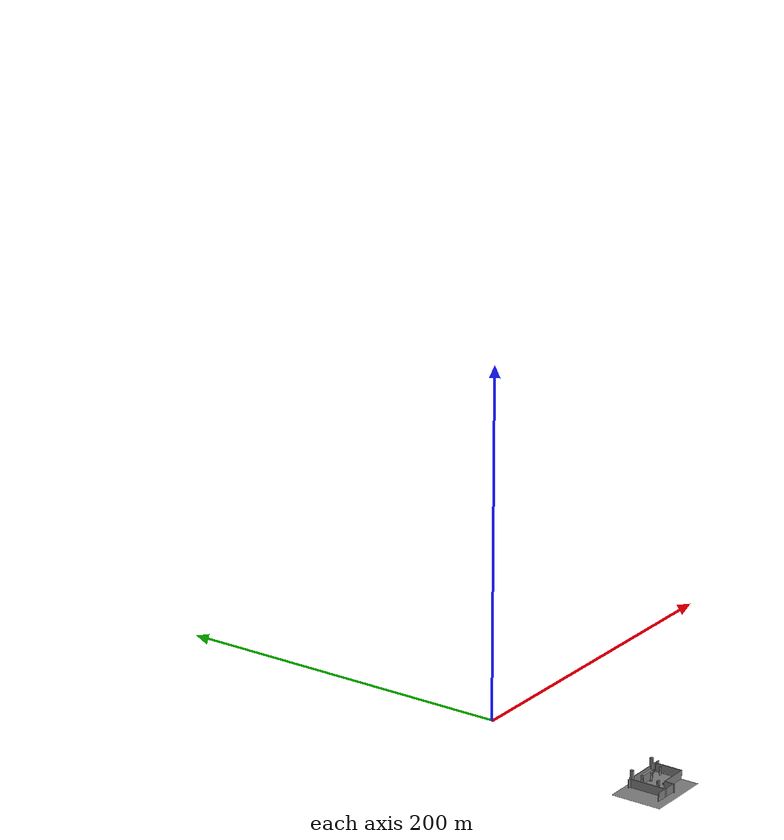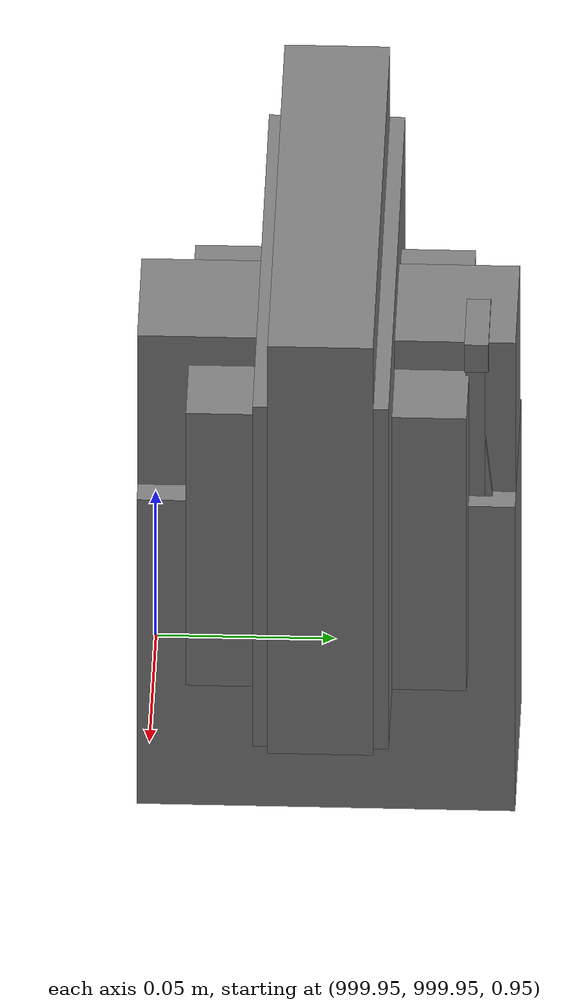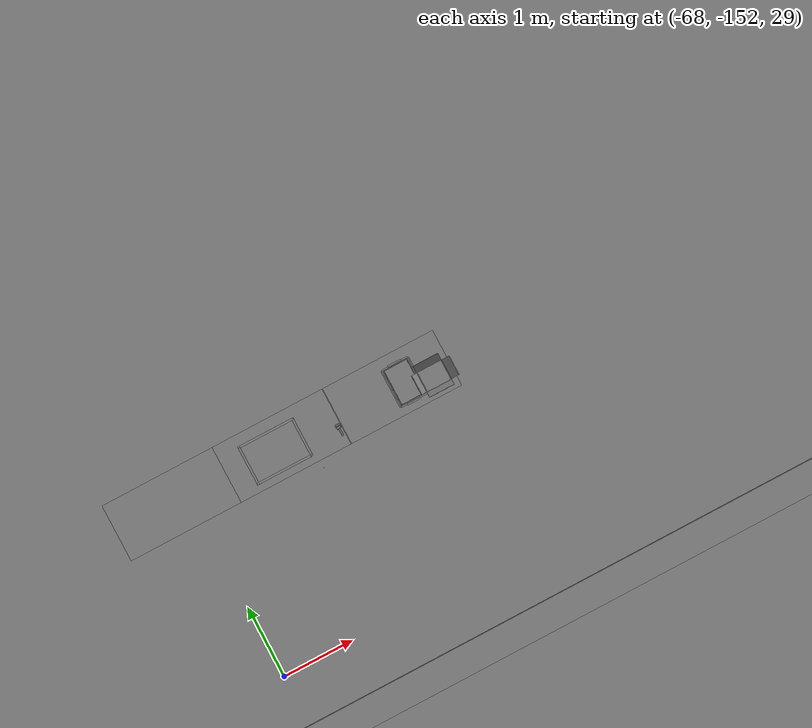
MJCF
<mujoco>
    <option gravity="0.000000000 0.000000000 -9.810000420" timestep="0.0049999999" integrator="implicitfast" density="1.225" viscosity="1.8000001e-05" noslip_iterations="10" iterations="100" sdf_iterations="50">
        <flag multiccd="disable"/>
    </option>
    <size memory="1000M"/>
    <compiler coordinate="local"/>
    <worldbody>
        <light cutoff="30" pos="0 1 1" dir="0 -1 -2"/>
        <light cutoff="30" pos="0 -1 1" dir="0 1 -2"/>
        <body pos="-64.866622925 -149.383972168 30.183746338" euler="89.999984741 89.999946594 0.000000000" name="openloong_gripper_2f85_fix_base_usda_bluebox_01">
            <geom contype="1" conaffinity="1" density="1000" type="box" material="" rgba="0.500000000 0.500000000 0.500000000 1.000000000" solimp="0.899999976 0.949999988 0.001000000" friction="1.000000000 0.005000000 0.000100000" solref="0.020000000 1.000000000" margin="0" condim="3" group="0" pos="0.276580811 0.187225342 0.000068665" quat="0.707106948 0.000077471 0.707106352 0.000077486" size="0.100000001 0.057999998 0.010000000" name="openloong_gripper_2f85_fix_base_usda_geom_09FB6DC2_A669_4610_B9E4_6EB0CFBE29BF"/>
            <geom contype="1" conaffinity="1" density="1000" type="box" material="" rgba="0.500000000 0.500000000 0.500000000 1.000000000" solimp="0.899999976 0.949999988 0.001000000" friction="1.000000000 0.005000000 0.000100000" solref="0.020000000 1.000000000" margin="0" condim="3" group="0" pos="0.000000000 0.002883911 0.000000000" quat="0.999999881 0.000000000 0.000000000 0.000000000" size="0.254000008 0.003000000 0.172000006" name="openloong_gripper_2f85_fix_base_usda_geom_5072D2AD_43F0_4C6C_900A_ED9F6B494E7A"/>
            <geom contype="1" conaffinity="1" density="1000" type="box" material="" rgba="0.500000000 0.500000000 0.500000000 1.000000000" solimp="0.899999976 0.949999988 0.001000000" friction="1.000000000 0.005000000 0.000100000" solref="0.020000000 1.000000000" margin="0" condim="3" group="0" pos="0.000000000 0.124874115 0.173484802" quat="0.999796331 0.020176515 -0.000000015 0.000000030" size="0.259999990 0.119999997 0.007000000" name="openloong_gripper_2f85_fix_base_usda_geom_E7DB65AF_BD7A_4FAB_A562_7AB235440530"/>
            <geom contype="1" conaffinity="1" density="1000" type="box" material="" rgba="0.500000000 0.500000000 0.500000000 1.000000000" solimp="0.899999976 0.949999988 0.001000000" friction="1.000000000 0.005000000 0.000100000" solref="0.020000000 1.000000000" margin="0" condim="3" group="0" pos="0.000000000 0.124874115 -0.173469543" quat="0.999796331 -0.020176545 -0.000000015 0.000000000" size="0.259999990 0.119999997 0.007000000" name="openloong_gripper_2f85_fix_base_usda_geom_5A839F28_7AB3_4316_AD26_0B1777C90DAD"/>
            <geom contype="1" conaffinity="1" density="1000" type="box" material="" rgba="0.500000000 0.500000000 0.500000000 1.000000000" solimp="0.899999976 0.949999988 0.001000000" friction="1.000000000 0.005000000 0.000100000" solref="0.020000000 1.000000000" margin="0" condim="3" group="0" pos="0.000000000 0.214008331 0.188980103" quat="0.999912977 0.013176724 0.000000015 0.000000000" size="0.259999990 0.029999999 0.012500000" name="openloong_gripper_2f85_fix_base_usda_geom_5C2CD066_B3B9_4595_B325_08D6B1512275"/>
            <geom contype="1" conaffinity="1" density="1000" type="box" material="" rgba="0.500000000 0.500000000 0.500000000 1.000000000" solimp="0.899999976 0.949999988 0.001000000" friction="1.000000000 0.005000000 0.000100000" solref="0.020000000 1.000000000" margin="0" condim="3" group="0" pos="-0.258361816 0.125289917 0.001876831" quat="0.702796936 -0.020792112 0.710783124 0.020769298" size="0.189999998 0.119999997 0.009000000" name="openloong_gripper_2f85_fix_base_usda_geom_4D769D8B_053D_437F_AD60_2D92FEAA5153"/>
            <geom contype="1" conaffinity="1" density="1000" type="box" material="" rgba="0.500000000 0.500000000 0.500000000 1.000000000" solimp="0.899999976 0.949999988 0.001000000" friction="1.000000000 0.005000000 0.000100000" solref="0.020000000 1.000000000" margin="0" condim="3" group="0" pos="0.000000000 0.214008331 -0.188980103" quat="0.999912977 -0.013176769 0.000000030 0.000000015" size="0.259999990 0.029999999 0.012500000" name="openloong_gripper_2f85_fix_base_usda_geom_3BB5033D_CA59_4309_9766_D0655F4BFA86"/>
            <geom contype="1" conaffinity="1" density="1000" type="box" material="" rgba="0.500000000 0.500000000 0.500000000 1.000000000" solimp="0.899999976 0.949999988 0.001000000" friction="1.000000000 0.005000000 0.000100000" solref="0.020000000 1.000000000" margin="0" condim="3" group="0" pos="-0.276611328 0.187225342 0.000068665" quat="0.707106650 0.000077441 0.707106709 0.000077456" size="0.100000001 0.057999998 0.010000000" name="openloong_gripper_2f85_fix_base_usda_geom_BA57BB51_4553_4FCF_A32F_BFBA8520448B"/>
            <geom contype="1" conaffinity="1" density="1000" type="box" material="" rgba="0.500000000 0.500000000 0.500000000 1.000000000" solimp="0.899999976 0.949999988 0.001000000" friction="1.000000000 0.005000000 0.000100000" solref="0.020000000 1.000000000" margin="0" condim="3" group="0" pos="0.258331299 0.125289917 0.001876831" quat="0.702851415 0.018856421 0.710823774 -0.019329369" size="0.189999998 0.119999997 0.009000000" name="openloong_gripper_2f85_fix_base_usda_geom_89932CE5_7BD5_484E_B67B_C11F37FB4B5A"/>
            <freejoint name="openloong_gripper_2f85_fix_base_usda_bluebox_01_joint"/>
            <site size="0.005000000 0.005000000 0.005000000" rgba="0.500000000 0.500000000 0.500000000 1.000000000" pos="0.000000000 0.000000000 0.000000000" quat="0.999961913 0.008726534 0.000000000 0.000000000" group="0" type="sphere" name="openloong_gripper_2f85_fix_base_usda_bluebox_01site"/>
        </body>
        <body pos="-64.496299744 -149.491867065 30.235729218" euler="0.000000000 0.000000000 89.999946594" name="openloong_gripper_2f85_fix_base_usda_cardboardbox_01">
            <geom contype="1" conaffinity="1" density="1000" type="box" material="" rgba="0.500000000 0.500000000 0.500000000 1.000000000" solimp="0.899999976 0.949999988 0.001000000" friction="1.000000000 0.005000000 0.000100000" solref="0.020000000 1.000000000" margin="0" condim="3" group="0" pos="-0.003166199 -0.004086494 0.005052090" quat="1.000000000 0.000000000 0.000000000 0.000000000" size="0.142499998 0.177500010 0.005000000" name="openloong_gripper_2f85_fix_base_usda_geom_0AC8348C_A989_4AF1_AE65_293FD5132643"/>
            <geom contype="1" conaffinity="1" density="1000" type="box" material="" rgba="0.500000000 0.500000000 0.500000000 1.000000000" solimp="0.899999976 0.949999988 0.001000000" friction="1.000000000 0.005000000 0.000100000" solref="0.020000000 1.000000000" margin="0" condim="3" group="0" pos="-0.003166199 0.170316696 0.150570869" quat="1.000000000 0.000000000 0.000000000 0.000000000" size="0.142499998 0.005000000 0.149999991" name="openloong_gripper_2f85_fix_base_usda_geom_ED885A2B_1A1B_4256_935B_2BF8CBE479EE"/>
            <geom contype="1" conaffinity="1" density="1000" type="box" material="" rgba="0.500000000 0.500000000 0.500000000 1.000000000" solimp="0.899999976 0.949999988 0.001000000" friction="1.000000000 0.005000000 0.000100000" solref="0.020000000 1.000000000" margin="0" condim="3" group="0" pos="-0.147399902 -0.005307198 0.150570869" quat="1.000000000 0.000000000 0.000000000 0.000000000" size="0.005000000 0.177500010 0.149999991" name="openloong_gripper_2f85_fix_base_usda_geom_221348F6_CC52_4325_84F0_038E9D71425A"/>
            <geom contype="1" conaffinity="1" density="1000" type="box" material="" rgba="0.500000000 0.500000000 0.500000000 1.000000000" solimp="0.899999976 0.949999988 0.001000000" friction="1.000000000 0.005000000 0.000100000" solref="0.020000000 1.000000000" margin="0" condim="3" group="0" pos="0.140275955 -0.005307198 0.150570869" quat="1.000000000 0.000000000 0.000000000 0.000000000" size="0.005000000 0.177500010 0.149999991" name="openloong_gripper_2f85_fix_base_usda_geom_C69F2A8D_6773_41E3_B36D_5E4FF7BD19B0"/>
            <geom contype="1" conaffinity="1" density="1000" type="box" material="" rgba="0.500000000 0.500000000 0.500000000 1.000000000" solimp="0.899999976 0.949999988 0.001000000" friction="1.000000000 0.005000000 0.000100000" solref="0.020000000 1.000000000" margin="0" condim="3" group="0" pos="-0.003166199 -0.181550980 0.150570869" quat="1.000000000 0.000000000 0.000000000 0.000000000" size="0.142499998 0.005000000 0.149999991" name="openloong_gripper_2f85_fix_base_usda_geom_68D1D36D_C7BE_470D_B037_43D172502B9F"/>
            <freejoint name="openloong_gripper_2f85_fix_base_usda_cardboardbox_01_joint"/>
            <site size="0.005000000 0.005000000 0.005000000" rgba="0.500000000 0.500000000 0.500000000 1.000000000" pos="0.000000000 0.000000000 0.000000000" quat="0.999961913 0.008726535 0.000000000 0.000000000" group="0" type="sphere" name="openloong_gripper_2f85_fix_base_usda_site_01FDEC79_D415_4C76_A5E8_DD67019067B4"/>
            <body pos="0.139160156 -0.004048347 0.301930904" euler="-179.999954224 49.383502960 179.999954224" name="openloong_gripper_2f85_fix_base_usda_A1_006">
                <geom contype="1" conaffinity="1" density="1000" type="box" material="" rgba="0.500000000 0.500000000 0.500000000 1.000000000" solimp="0.899999976 0.949999988 0.001000000" friction="1.000000000 0.005000000 0.000100000" solref="0.020000000 1.000000000" margin="0" condim="3" group="0" pos="-0.071587563 0.000009537 0.001745224" quat="0.999999881 0.000000000 0.000000000 0.000000000" size="0.071249999 0.179999992 0.002500000" name="openloong_gripper_2f85_fix_base_usda_geom_A71963AE_9438_44F0_A151_B192E333227A"/>
                <joint armature="0" stiffness="0.07" damping="0.0099999998" axis="0.000000 1.000000 0.000000" type="hinge" name="openloong_gripper_2f85_fix_base_usda_A1_006"/>
            </body>
            <body pos="-0.145902634 -0.004086494 0.301938057" euler="-180.000000000 -60.000011444 -180.000000000" name="openloong_gripper_2f85_fix_base_usda_A2_006">
                <geom contype="1" conaffinity="1" density="1000" type="box" material="" rgba="0.500000000 0.500000000 0.500000000 1.000000000" solimp="0.899999976 0.949999988 0.001000000" friction="1.000000000 0.005000000 0.000100000" solref="0.020000000 1.000000000" margin="0" condim="3" group="0" pos="0.071268082 0.000009537 0.002717972" quat="0.000002921 0.000000000 -0.000000030 0.999999881" size="0.071249999 0.179999992 0.002500000" name="openloong_gripper_2f85_fix_base_usda_geom_FC91BC43_814F_447C_B621_AF8ED38B5423"/>
                <joint armature="0" stiffness="0.07" damping="0.0099999998" axis="0.000000 1.000000 0.000000" type="hinge" name="openloong_gripper_2f85_fix_base_usda_A2_006"/>
            </body>
            <body pos="-0.003385544 0.175991058 0.301930904" euler="-125.858116150 -0.000004561 0.000002331" name="openloong_gripper_2f85_fix_base_usda_B2_006">
                <geom contype="1" conaffinity="1" density="1000" type="box" material="" rgba="0.500000000 0.500000000 0.500000000 1.000000000" solimp="0.899999976 0.949999988 0.001000000" friction="1.000000000 0.005000000 0.000100000" solref="0.020000000 1.000000000" margin="0" condim="3" group="0" pos="0.000009537 -0.070939064 -0.002470016" quat="0.999614120 0.027776197 -0.000000015 0.000000030" size="0.137500003 0.064999998 0.005000000" name="openloong_gripper_2f85_fix_base_usda_geom_2A5EB334_7BF6_45C3_BD8F_1F2BB91C0B40"/>
                <joint armature="0" stiffness="0.07" damping="0.0099999998" axis="1.000000 0.000000 0.000000" type="hinge" name="openloong_gripper_2f85_fix_base_usda_B2_006"/>
            </body>
            <body pos="-0.003385544 -0.184140205 0.301938057" euler="147.805557251 0.000000000 0.000000000" name="openloong_gripper_2f85_fix_base_usda_B1_006">
                <geom contype="1" conaffinity="1" density="1000" type="box" material="" rgba="0.500000000 0.500000000 0.500000000 1.000000000" solimp="0.899999976 0.949999988 0.001000000" friction="1.000000000 0.005000000 0.000100000" solref="0.020000000 1.000000000" margin="0" condim="3" group="0" pos="-0.000028610 0.070202351 -0.002703667" quat="0.999614179 -0.027776167 0.000000000 0.000000000" size="0.137500003 0.064999998 0.005000000" name="openloong_gripper_2f85_fix_base_usda_geom_12E6CA86_51AC_462E_80FB_29CB1453B964"/>
                <joint armature="0" stiffness="0.07" damping="0.0099999998" axis="1.000000 0.000000 0.000000" type="hinge" name="openloong_gripper_2f85_fix_base_usda_B1_006"/>
            </body>
        </body>
        <body pos="-65.882858276 -149.481979370 30.229999542" euler="-64.487716675 0.000000000 0.000000000" name="openloong_gripper_2f85_fix_base_usda_Barcode">
            <geom contype="1" conaffinity="1" density="1000" type="box" material="" rgba="0.500000000 0.500000000 0.500000000 1.000000000" solimp="0.899999976 0.949999988 0.001000000" friction="1.000000000 0.005000000 0.000100000" solref="0.020000000 1.000000000" margin="0" condim="3" group="0" pos="0.000000000 0.013038635 0.001419067" quat="0.000000000 0.000000000 0.000000000 1.000000119" size="0.034000002 0.010000000 0.017999999" name="openloong_gripper_2f85_fix_base_usda_geom_945933C1_693E_4BE4_9B5B_FE60EE5A5CF9"/>
            <geom contype="1" conaffinity="1" density="1000" type="box" material="" rgba="0.500000000 0.500000000 0.500000000 1.000000000" solimp="0.899999976 0.949999988 0.001000000" friction="1.000000000 0.005000000 0.000100000" solref="0.020000000 1.000000000" margin="0" condim="3" group="0" pos="0.000000000 -0.035301208 -0.007095337" quat="0.000000000 0.000000000 -0.043619365 0.999048233" size="0.028999999 0.010000000 0.020000000" name="openloong_gripper_2f85_fix_base_usda_geom_184619A7_B1F6_4251_95F5_23C5752934C8"/>
            <geom contype="1" conaffinity="1" density="1000" type="box" material="" rgba="0.500000000 0.500000000 0.500000000 1.000000000" solimp="0.899999976 0.949999988 0.001000000" friction="1.000000000 0.005000000 0.000100000" solref="0.020000000 1.000000000" margin="0" condim="3" group="0" pos="0.000000000 -0.043411255 -0.011749268" quat="0.922262907 0.386563420 0.000000000 0.000000000" size="0.026000001 0.010000000 0.020000000" name="openloong_gripper_2f85_fix_base_usda_geom_F5BAD53C_F107_414D_BCD4_4F813EB0C97B"/>
            <geom contype="1" conaffinity="1" density="1000" type="box" material="" rgba="0.500000000 0.500000000 0.500000000 1.000000000" solimp="0.899999976 0.949999988 0.001000000" friction="1.000000000 0.005000000 0.000100000" solref="0.020000000 1.000000000" margin="0" condim="3" group="0" pos="0.000000000 -0.016967773 -0.031860352" quat="0.000000000 0.000000000 0.000000000 1.000000119" size="0.008000000 0.010000000 0.013000000" name="openloong_gripper_2f85_fix_base_usda_geom_17E73C94_9927_4954_A6DC_C6A48C452E27"/>
            <geom contype="1" conaffinity="1" density="1000" type="box" material="" rgba="0.500000000 0.500000000 0.500000000 1.000000000" solimp="0.899999976 0.949999988 0.001000000" friction="1.000000000 0.005000000 0.000100000" solref="0.020000000 1.000000000" margin="0" condim="3" group="0" pos="0.000000000 -0.001869202 0.000312805" quat="0.953716993 0.300705761 0.000000000 0.000000000" size="0.032000002 0.010000000 0.018999999" name="openloong_gripper_2f85_fix_base_usda_geom_C659AC32_0369_49E0_B189_E25B802C89D6"/>
            <geom contype="1" conaffinity="1" density="1000" type="box" material="" rgba="0.500000000 0.500000000 0.500000000 1.000000000" solimp="0.899999976 0.949999988 0.001000000" friction="1.000000000 0.005000000 0.000100000" solref="0.020000000 1.000000000" margin="0" condim="3" group="0" pos="0.000000000 -0.019531250 -0.003173828" quat="0.953716993 0.300705761 0.000000000 0.000000000" size="0.030999999 0.010000000 0.020000000" name="openloong_gripper_2f85_fix_base_usda_geom_77973CAE_6ACB_403A_8563_9E5094134000"/>
            <geom contype="1" conaffinity="1" density="1000" type="box" material="" rgba="0.500000000 0.500000000 0.500000000 1.000000000" solimp="0.899999976 0.949999988 0.001000000" friction="1.000000000 0.005000000 0.000100000" solref="0.020000000 1.000000000" margin="0" condim="3" group="0" pos="0.000000000 -0.035301208 -0.007095337" quat="0.953716993 0.300705761 0.000000000 0.000000000" size="0.028999999 0.010000000 0.020000000" name="openloong_gripper_2f85_fix_base_usda_geom_2DC82B09_CD64_40E0_A1CC_A29E52A42DCA"/>
            <geom contype="1" conaffinity="1" density="1000" type="box" material="" rgba="0.500000000 0.500000000 0.500000000 1.000000000" solimp="0.899999976 0.949999988 0.001000000" friction="1.000000000 0.005000000 0.000100000" solref="0.020000000 1.000000000" margin="0" condim="3" group="0" pos="0.000000000 -0.042617798 -0.071121216" quat="0.000000000 0.000000000 0.000000000 1.000000119" size="0.013000000 0.021000000 0.059999999" name="openloong_gripper_2f85_fix_base_usda_geom_A2733308_9A31_419D_A75D_97AF72B56FA7"/>
            <freejoint name="openloong_gripper_2f85_fix_base_usda_Barcode_joint"/>
            <site size="0.005000000 0.005000000 0.005000000" rgba="0.500000000 0.500000000 0.500000000 1.000000000" pos="0.000000000 0.000000000 0.000000000" quat="1.000000000 0.000000000 0.000000000 0.000000000" group="0" type="sphere" name="openloong_gripper_2f85_fix_base_usda_Barcode_site"/>
        </body>
        <body pos="-66.745018005 -149.392349243 30.184000015" euler="0.000000000 0.000000000 89.999946594" name="[22330396903471]_Basket_01">
            <geom contype="1" conaffinity="1" density="1000" type="box" material="" rgba="0.500000000 0.500000000 0.500000000 1.000000000" solimp="0.899999976 0.949999988 0.001000000" friction="1.000000000 0.005000000 0.000100000" solref="0.020000000 1.000000000" margin="0" condim="3" group="0" pos="-0.052425385 0.389207840 0.089787483" quat="0.707107008 0.000000000 0.000000000 0.707106411" size="0.014249999 0.014249999 0.059999999" name="[22330396903471]_geom_5F43E875_7EF2_4C47_B6F0_E16AEA79C616"/>
            <geom contype="1" conaffinity="1" density="1000" type="box" material="" rgba="0.500000000 0.500000000 0.500000000 1.000000000" solimp="0.899999976 0.949999988 0.001000000" friction="1.000000000 0.005000000 0.000100000" solref="0.020000000 1.000000000" margin="0" condim="3" group="0" pos="0.264015198 -0.133043289 0.089787483" quat="0.707107008 0.000000000 0.000000000 0.707106411" size="0.014249999 0.014249999 0.059999999" name="[22330396903471]_geom_51CFC67A_52EA_4301_B48A_4E8CB436A35F"/>
            <geom contype="1" conaffinity="1" density="1000" type="box" material="" rgba="0.500000000 0.500000000 0.500000000 1.000000000" solimp="0.899999976 0.949999988 0.001000000" friction="1.000000000 0.005000000 0.000100000" solref="0.020000000 1.000000000" margin="0" condim="3" group="0" pos="-0.264015198 -0.265548706 0.089793205" quat="0.707107008 0.000000000 0.000000000 0.707106411" size="0.014249999 0.014249999 0.059999999" name="[22330396903471]_geom_395431A8_BF5F_4894_AFB2_8AC81CF912B7"/>
            <geom contype="1" conaffinity="1" density="1000" type="box" material="" rgba="0.500000000 0.500000000 0.500000000 1.000000000" solimp="0.899999976 0.949999988 0.001000000" friction="1.000000000 0.005000000 0.000100000" solref="0.020000000 1.000000000" margin="0" condim="3" group="0" pos="-0.160263062 -0.389322281 0.089793205" quat="0.707107008 0.000000000 0.000000000 0.707106411" size="0.014249999 0.014249999 0.059999999" name="[22330396903471]_geom_84C85023_654A_4B72_B29E_45A04BD28A9B"/>
            <geom contype="1" conaffinity="1" density="1000" type="box" material="" rgba="0.500000000 0.500000000 0.500000000 1.000000000" solimp="0.899999976 0.949999988 0.001000000" friction="1.000000000 0.005000000 0.000100000" solref="0.020000000 1.000000000" margin="0" condim="3" group="0" pos="0.162265778 -0.389322281 0.089787483" quat="0.707107008 0.000000000 0.000000000 0.707106411" size="0.014249999 0.014249999 0.059999999" name="[22330396903471]_geom_77C256B7_D4A7_4655_BD2F_80B30E1DF161"/>
            <geom contype="1" conaffinity="1" density="1000" type="box" material="" rgba="0.500000000 0.500000000 0.500000000 1.000000000" solimp="0.899999976 0.949999988 0.001000000" friction="1.000000000 0.005000000 0.000100000" solref="0.020000000 1.000000000" margin="0" condim="3" group="0" pos="0.264015198 0.389207840 0.089787483" quat="0.707107008 0.000000000 0.000000000 0.707106411" size="0.014249999 0.014249999 0.059999999" name="[22330396903471]_geom_E3EF3A5B_6E20_4C69_A101_879AFC7C6F74"/>
            <geom contype="1" conaffinity="1" density="1000" type="box" material="" rgba="0.500000000 0.500000000 0.500000000 1.000000000" solimp="0.899999976 0.949999988 0.001000000" friction="1.000000000 0.005000000 0.000100000" solref="0.020000000 1.000000000" margin="0" condim="3" group="0" pos="-0.264015198 -0.133043289 0.089793205" quat="0.707107008 0.000000000 0.000000000 0.707106411" size="0.014249999 0.014249999 0.059999999" name="[22330396903471]_geom_0A7FBE3E_A676_40B0_A847_BF0BCFF19007"/>
            <geom contype="1" conaffinity="1" density="1000" type="box" material="" rgba="0.500000000 0.500000000 0.500000000 1.000000000" solimp="0.899999976 0.949999988 0.001000000" friction="1.000000000 0.005000000 0.000100000" solref="0.020000000 1.000000000" margin="0" condim="3" group="0" pos="-0.264026642 0.269256592 0.089793205" quat="0.707107008 0.000000000 0.000000000 0.707106411" size="0.014249999 0.014249999 0.059999999" name="[22330396903471]_geom_3CA6946C_9089_444B_8FCB_63E864F82CE1"/>
            <geom contype="1" conaffinity="1" density="1000" type="box" material="" rgba="0.500000000 0.500000000 0.500000000 1.000000000" solimp="0.899999976 0.949999988 0.001000000" friction="1.000000000 0.005000000 0.000100000" solref="0.020000000 1.000000000" margin="0" condim="3" group="0" pos="0.054462433 0.389207840 0.089787483" quat="0.707107008 0.000000000 0.000000000 0.707106411" size="0.014249999 0.014249999 0.059999999" name="[22330396903471]_geom_804847C8_CAB8_494F_94F7_8DDA878F8D7D"/>
            <geom contype="1" conaffinity="1" density="1000" type="box" material="" rgba="0.500000000 0.500000000 0.500000000 1.000000000" solimp="0.899999976 0.949999988 0.001000000" friction="1.000000000 0.005000000 0.000100000" solref="0.020000000 1.000000000" margin="0" condim="3" group="0" pos="0.054462433 -0.389322281 0.089787483" quat="0.707107008 0.000000000 0.000000000 0.707106411" size="0.014249999 0.014249999 0.059999999" name="[22330396903471]_geom_ECF19555_D366_4951_815F_173D0310D0DE"/>
            <geom contype="1" conaffinity="1" density="1000" type="box" material="" rgba="0.500000000 0.500000000 0.500000000 1.000000000" solimp="0.899999976 0.949999988 0.001000000" friction="1.000000000 0.005000000 0.000100000" solref="0.020000000 1.000000000" margin="0" condim="3" group="0" pos="0.264015198 0.269256592 0.089793205" quat="0.707107008 0.000000000 0.000000000 0.707106411" size="0.014249999 0.014249999 0.059999999" name="[22330396903471]_geom_4A738929_5FCC_4D36_8897_82075E64A9A2"/>
            <geom contype="1" conaffinity="1" density="1000" type="box" material="" rgba="0.500000000 0.500000000 0.500000000 1.000000000" solimp="0.899999976 0.949999988 0.001000000" friction="1.000000000 0.005000000 0.000100000" solref="0.020000000 1.000000000" margin="0" condim="3" group="0" pos="0.264015198 -0.389322281 0.089787483" quat="0.707107008 0.000000000 0.000000000 0.707106411" size="0.014249999 0.014249999 0.059999999" name="[22330396903471]_geom_C6C57B98_7F86_4E47_85A8_ACA5FFCEA524"/>
            <geom contype="1" conaffinity="1" density="1000" type="box" material="" rgba="0.500000000 0.500000000 0.500000000 1.000000000" solimp="0.899999976 0.949999988 0.001000000" friction="1.000000000 0.005000000 0.000100000" solref="0.020000000 1.000000000" margin="0" condim="3" group="0" pos="0.000000000 0.000000000 0.015998840" quat="0.707107008 0.000000000 0.000000000 0.707106411" size="0.403499991 0.279000014 0.015750000" name="[22330396903471]_geom_453C6BA7_2C66_4805_93E4_710179A0380F"/>
            <geom contype="1" conaffinity="1" density="1000" type="box" material="" rgba="0.500000000 0.500000000 0.500000000 1.000000000" solimp="0.899999976 0.949999988 0.001000000" friction="1.000000000 0.005000000 0.000100000" solref="0.020000000 1.000000000" margin="0" condim="3" group="0" pos="0.000000000 -0.389476776 0.163619041" quat="0.707107008 0.000000000 0.000000000 0.707106411" size="0.015000000 0.277500004 0.015750000" name="[22330396903471]_geom_BE51B46F_F52F_4C82_99FE_71A7DDF411AB"/>
            <geom contype="1" conaffinity="1" density="1000" type="box" material="" rgba="0.500000000 0.500000000 0.500000000 1.000000000" solimp="0.899999976 0.949999988 0.001000000" friction="1.000000000 0.005000000 0.000100000" solref="0.020000000 1.000000000" margin="0" condim="3" group="0" pos="0.162265778 0.389207840 0.089787483" quat="0.707107008 0.000000000 0.000000000 0.707106411" size="0.014249999 0.014249999 0.059999999" name="[22330396903471]_geom_5146BEAF_FAC1_4BB7_92B5_E70262E5F18F"/>
            <geom contype="1" conaffinity="1" density="1000" type="box" material="" rgba="0.500000000 0.500000000 0.500000000 1.000000000" solimp="0.899999976 0.949999988 0.001000000" friction="1.000000000 0.005000000 0.000100000" solref="0.020000000 1.000000000" margin="0" condim="3" group="0" pos="0.000000000 0.389471054 0.163619041" quat="0.707107008 0.000000000 0.000000000 0.707106411" size="0.015000000 0.277500004 0.015750000" name="[22330396903471]_geom_66B4B5EA_C21E_4604_8643_3B677AC2BB39"/>
            <geom contype="1" conaffinity="1" density="1000" type="box" material="" rgba="0.500000000 0.500000000 0.500000000 1.000000000" solimp="0.899999976 0.949999988 0.001000000" friction="1.000000000 0.005000000 0.000100000" solref="0.020000000 1.000000000" margin="0" condim="3" group="0" pos="-0.263511658 0.000000000 0.163619041" quat="0.707107008 0.000000000 0.000000000 0.707106411" size="0.403499991 0.015000000 0.015750000" name="[22330396903471]_geom_6DE98E6C_6223_430A_A415_68EB2A141013"/>
            <geom contype="1" conaffinity="1" density="1000" type="box" material="" rgba="0.500000000 0.500000000 0.500000000 1.000000000" solimp="0.899999976 0.949999988 0.001000000" friction="1.000000000 0.005000000 0.000100000" solref="0.020000000 1.000000000" margin="0" condim="3" group="0" pos="-0.264015198 0.141334534 0.089793205" quat="0.707107008 0.000000000 0.000000000 0.707106411" size="0.014249999 0.014249999 0.059999999" name="[22330396903471]_geom_B228E387_D6D3_4CB5_967C_53E73B91AC38"/>
            <geom contype="1" conaffinity="1" density="1000" type="box" material="" rgba="0.500000000 0.500000000 0.500000000 1.000000000" solimp="0.899999976 0.949999988 0.001000000" friction="1.000000000 0.005000000 0.000100000" solref="0.020000000 1.000000000" margin="0" condim="3" group="0" pos="0.264015198 -0.265548706 0.089787483" quat="0.707107008 0.000000000 0.000000000 0.707106411" size="0.014249999 0.014249999 0.059999999" name="[22330396903471]_geom_A1408EDB_C873_43D9_B7FD_9C398D6014F4"/>
            <geom contype="1" conaffinity="1" density="1000" type="box" material="" rgba="0.500000000 0.500000000 0.500000000 1.000000000" solimp="0.899999976 0.949999988 0.001000000" friction="1.000000000 0.005000000 0.000100000" solref="0.020000000 1.000000000" margin="0" condim="3" group="0" pos="-0.160263062 0.389207840 0.089787483" quat="0.707107008 0.000000000 0.000000000 0.707106411" size="0.014249999 0.014249999 0.059999999" name="[22330396903471]_geom_D25B0D4B_0C00_45DC_800F_FE5E26A78669"/>
            <geom contype="1" conaffinity="1" density="1000" type="box" material="" rgba="0.500000000 0.500000000 0.500000000 1.000000000" solimp="0.899999976 0.949999988 0.001000000" friction="1.000000000 0.005000000 0.000100000" solref="0.020000000 1.000000000" margin="0" condim="3" group="0" pos="-0.052425385 -0.389322281 0.089787483" quat="0.707107008 0.000000000 0.000000000 0.707106411" size="0.014249999 0.014249999 0.059999999" name="[22330396903471]_geom_618F05FD_FF8A_4C5C_A497_74E5F012EC34"/>
            <geom contype="1" conaffinity="1" density="1000" type="box" material="" rgba="0.500000000 0.500000000 0.500000000 1.000000000" solimp="0.899999976 0.949999988 0.001000000" friction="1.000000000 0.005000000 0.000100000" solref="0.020000000 1.000000000" margin="0" condim="3" group="0" pos="-0.264026642 -0.389322281 0.089793205" quat="0.707107008 0.000000000 0.000000000 0.707106411" size="0.014249999 0.014249999 0.059999999" name="[22330396903471]_geom_D4D45847_F34B_4DB2_A4A0_BF8164FD9026"/>
            <geom contype="1" conaffinity="1" density="1000" type="box" material="" rgba="0.500000000 0.500000000 0.500000000 1.000000000" solimp="0.899999976 0.949999988 0.001000000" friction="1.000000000 0.005000000 0.000100000" solref="0.020000000 1.000000000" margin="0" condim="3" group="0" pos="0.264015198 0.141334534 0.089787483" quat="0.707107008 0.000000000 0.000000000 0.707106411" size="0.014249999 0.014249999 0.059999999" name="[22330396903471]_geom_1D8474C4_A304_4C44_8425_F3CFE08B36CC"/>
            <geom contype="1" conaffinity="1" density="1000" type="box" material="" rgba="0.500000000 0.500000000 0.500000000 1.000000000" solimp="0.899999976 0.949999988 0.001000000" friction="1.000000000 0.005000000 0.000100000" solref="0.020000000 1.000000000" margin="0" condim="3" group="0" pos="-0.264015198 0.389207840 0.089793205" quat="0.707107008 0.000000000 0.000000000 0.707106411" size="0.014249999 0.014249999 0.059999999" name="[22330396903471]_geom_63A4B022_BA1C_41FA_BF37_061159CFC329"/>
            <geom contype="1" conaffinity="1" density="1000" type="box" material="" rgba="0.500000000 0.500000000 0.500000000 1.000000000" solimp="0.899999976 0.949999988 0.001000000" friction="1.000000000 0.005000000 0.000100000" solref="0.020000000 1.000000000" margin="0" condim="3" group="0" pos="0.264015198 0.004480362 0.089787483" quat="0.707107008 0.000000000 0.000000000 0.707106411" size="0.014249999 0.014249999 0.059999999" name="[22330396903471]_geom_BB675D66_9518_4995_99ED_23502343FEEE"/>
            <geom contype="1" conaffinity="1" density="1000" type="box" material="" rgba="0.500000000 0.500000000 0.500000000 1.000000000" solimp="0.899999976 0.949999988 0.001000000" friction="1.000000000 0.005000000 0.000100000" solref="0.020000000 1.000000000" margin="0" condim="3" group="0" pos="0.263694763 -0.000011444 0.163619041" quat="0.707107008 0.000000000 0.000000000 0.707106411" size="0.403499991 0.015000000 0.015750000" name="[22330396903471]_geom_E23C25B8_F18C_4CF1_B8C1_D7DF210E7548"/>
            <geom contype="1" conaffinity="1" density="1000" type="box" material="" rgba="0.500000000 0.500000000 0.500000000 1.000000000" solimp="0.899999976 0.949999988 0.001000000" friction="1.000000000 0.005000000 0.000100000" solref="0.020000000 1.000000000" margin="0" condim="3" group="0" pos="-0.264015198 0.004480362 0.089793205" quat="0.707107008 0.000000000 0.000000000 0.707106411" size="0.014249999 0.014249999 0.059999999" name="[22330396903471]_geom_FE781C49_8185_4FEF_883B_3E86EB891F1F"/>
            <freejoint name="[22330396903471]_joint_CEE9A420_1381_469B_AD44_A30DACA19E08"/>
        </body>
        <body pos="0.000000000 0.000000000 0.000000000" euler="0.000000000 0.000000000 0.000000000" name="Static Objects_Static Objects">
            <geom contype="1" conaffinity="1" density="1000" type="box" material="" rgba="0.500000000 0.500000000 0.500000000 1.000000000" solimp="0.899999976 0.949999988 0.001000000" friction="1.000000000 0.005000000 0.000100000" solref="0.020000000 1.000000000" margin="0" condim="3" group="0" pos="-67.544113159 -149.365814209 29.727830887" quat="0.500000417 0.499999970 0.499999553 0.499999970" size="0.381000012 0.319999993 0.041000001" name="Static Objects_geom_2418674D_02D5_4C96_B65E_8351E969327A"/>
            <geom contype="1" conaffinity="1" density="1000" type="box" material="" rgba="0.500000000 0.500000000 0.500000000 1.000000000" solimp="0.899999976 0.949999988 0.001000000" friction="1.000000000 0.005000000 0.000100000" solref="0.020000000 1.000000000" margin="0" condim="3" group="0" pos="-68.239501953 -149.365814209 30.086868286" quat="0.500000417 0.499999970 0.499999553 0.499999970" size="0.370999992 0.039500002 0.745000005" name="Static Objects_geom_F9CC14C4_9D64_4172_9A2F_798E175645E1"/>
            <geom contype="1" conaffinity="1" density="1000" type="box" material="" rgba="0.500000000 0.500000000 0.500000000 1.000000000" solimp="0.899999976 0.949999988 0.001000000" friction="1.000000000 0.005000000 0.000100000" solref="0.020000000 1.000000000" margin="0" condim="3" group="0" pos="-68.239501953 -149.365814209 30.147235870" quat="0.500000417 0.499999970 0.499999553 0.499999970" size="0.400000006 0.022000000 0.800000012" name="Static Objects_geom_D90751DE_4A35_42F6_90FD_287DAE668087"/>
            <geom contype="1" conaffinity="1" density="1000" type="box" material="" rgba="0.500000000 0.500000000 0.500000000 1.000000000" solimp="0.899999976 0.949999988 0.001000000" friction="1.000000000 0.005000000 0.000100000" solref="0.020000000 1.000000000" margin="0" condim="3" group="0" pos="-68.934890747 -149.365814209 29.727830887" quat="0.500000417 0.499999970 0.499999553 0.499999970" size="0.381000012 0.319999993 0.041000001" name="Static Objects_geom_2AEA906D_8678_4064_A355_130D85BC7479"/>
            <geom contype="1" conaffinity="1" density="1000" type="box" material="" rgba="0.500000000 0.500000000 0.500000000 1.000000000" solimp="0.899999976 0.949999988 0.001000000" friction="1.000000000 0.005000000 0.000100000" solref="0.020000000 1.000000000" margin="0" condim="3" group="0" pos="-68.239501953 -149.365814209 29.561563492" quat="0.500000417 0.499999970 0.499999553 0.499999970" size="0.020000000 0.022000000 0.660000026" name="Static Objects_geom_8E57FE1A_A49D_4624_855D_FB5E5868C564"/>
            <geom contype="1" conaffinity="1" density="1000" type="box" material="" rgba="0.500000000 0.500000000 0.500000000 1.000000000" solimp="0.899999976 0.949999988 0.001000000" friction="1.000000000 0.005000000 0.000100000" solref="0.020000000 1.000000000" margin="0" condim="3" group="0" pos="-65.945671082 -149.365814209 29.727830887" quat="0.500000417 0.499999970 0.499999553 0.499999970" size="0.381000012 0.319999993 0.041000001" name="Static Objects_geom_7EA03605_76A1_439F_B5D9_A08A29E2A460"/>
            <geom contype="1" conaffinity="1" density="1000" type="box" material="" rgba="0.500000000 0.500000000 0.500000000 1.000000000" solimp="0.899999976 0.949999988 0.001000000" friction="1.000000000 0.005000000 0.000100000" solref="0.020000000 1.000000000" margin="0" condim="3" group="0" pos="-66.641059875 -149.365814209 30.086868286" quat="0.500000417 0.499999970 0.499999553 0.499999970" size="0.370999992 0.039500002 0.745000005" name="Static Objects_geom_67578F35_3C22_4C52_AA2D_F7BE6AE5E35B"/>
            <geom contype="1" conaffinity="1" density="1000" type="box" material="" rgba="0.500000000 0.500000000 0.500000000 1.000000000" solimp="0.899999976 0.949999988 0.001000000" friction="1.000000000 0.005000000 0.000100000" solref="0.020000000 1.000000000" margin="0" condim="3" group="0" pos="-66.641059875 -149.365814209 30.147235870" quat="0.500000417 0.499999970 0.499999553 0.499999970" size="0.400000006 0.022000000 0.800000012" name="Static Objects_geom_EA33F1A9_5A05_470A_9444_C0359FAFD442"/>
            <geom contype="1" conaffinity="1" density="1000" type="box" material="" rgba="0.500000000 0.500000000 0.500000000 1.000000000" solimp="0.899999976 0.949999988 0.001000000" friction="1.000000000 0.005000000 0.000100000" solref="0.020000000 1.000000000" margin="0" condim="3" group="0" pos="-67.336448669 -149.365814209 29.727830887" quat="0.500000417 0.499999970 0.499999553 0.499999970" size="0.381000012 0.319999993 0.041000001" name="Static Objects_geom_ACE80000_509F_4DEF_80E9_435DEF4562F4"/>
            <geom contype="1" conaffinity="1" density="1000" type="box" material="" rgba="0.500000000 0.500000000 0.500000000 1.000000000" solimp="0.899999976 0.949999988 0.001000000" friction="1.000000000 0.005000000 0.000100000" solref="0.020000000 1.000000000" margin="0" condim="3" group="0" pos="-66.641059875 -149.365814209 29.561563492" quat="0.500000417 0.499999970 0.499999553 0.499999970" size="0.020000000 0.022000000 0.660000026" name="Static Objects_geom_D204BB52_A6D8_427F_8DF6_239FC65786E8"/>
            <geom contype="1" conaffinity="1" density="1000" type="box" material="" rgba="0.500000000 0.500000000 0.500000000 1.000000000" solimp="0.899999976 0.949999988 0.001000000" friction="1.000000000 0.005000000 0.000100000" solref="0.020000000 1.000000000" margin="0" condim="3" group="0" pos="-64.338577271 -149.365814209 29.727830887" quat="0.500000417 0.499999970 0.499999553 0.499999970" size="0.381000012 0.319999993 0.041000001" name="Static Objects_geom_B0AA8330_1214_4684_A6D9_E44CD6E5A39D"/>
            <geom contype="1" conaffinity="1" density="1000" type="box" material="" rgba="0.500000000 0.500000000 0.500000000 1.000000000" solimp="0.899999976 0.949999988 0.001000000" friction="1.000000000 0.005000000 0.000100000" solref="0.020000000 1.000000000" margin="0" condim="3" group="0" pos="-65.033966064 -149.365814209 30.086868286" quat="0.500000417 0.499999970 0.499999553 0.499999970" size="0.370999992 0.039500002 0.745000005" name="Static Objects_geom_3EAC7A1F_1878_42E9_8606_4CCD8D5CE967"/>
            <geom contype="1" conaffinity="1" density="1000" type="box" material="" rgba="0.500000000 0.500000000 0.500000000 1.000000000" solimp="0.899999976 0.949999988 0.001000000" friction="1.000000000 0.005000000 0.000100000" solref="0.020000000 1.000000000" margin="0" condim="3" group="0" pos="-65.033966064 -149.365814209 30.147235870" quat="0.500000417 0.499999970 0.499999553 0.499999970" size="0.400000006 0.022000000 0.800000012" name="Static Objects_geom_93B7EFC5_127A_4D58_8DE6_2DEF3A1C9C9F"/>
            <geom contype="1" conaffinity="1" density="1000" type="box" material="" rgba="0.500000000 0.500000000 0.500000000 1.000000000" solimp="0.899999976 0.949999988 0.001000000" friction="1.000000000 0.005000000 0.000100000" solref="0.020000000 1.000000000" margin="0" condim="3" group="0" pos="-65.729354858 -149.365814209 29.727830887" quat="0.500000417 0.499999970 0.499999553 0.499999970" size="0.381000012 0.319999993 0.041000001" name="Static Objects_geom_4B96313E_71EC_4EB3_87F6_7BA5E60BC4D8"/>
            <geom contype="1" conaffinity="1" density="1000" type="box" material="" rgba="0.500000000 0.500000000 0.500000000 1.000000000" solimp="0.899999976 0.949999988 0.001000000" friction="1.000000000 0.005000000 0.000100000" solref="0.020000000 1.000000000" margin="0" condim="3" group="0" pos="-65.033966064 -149.365814209 29.561563492" quat="0.500000417 0.499999970 0.499999553 0.499999970" size="0.020000000 0.022000000 0.660000026" name="Static Objects_geom_FEBA2F8F_19A7_4C6C_B70A_E2DDD7501B1F"/>
            <geom contype="1" conaffinity="1" density="1000" type="box" material="" rgba="0.500000000 0.500000000 0.500000000 1.000000000" solimp="0.899999976 0.949999988 0.001000000" friction="1.000000000 0.005000000 0.000100000" solref="0.020000000 1.000000000" margin="0" condim="3" group="0" pos="-61.754566193 -137.853729248 33.906845093" quat="0.707107067 0.000000000 0.000000000 0.707106471" size="0.759999990 0.759999990 4.500000000" name="Static Objects_geom_87D65F9D_B138_42A1_83A7_B320AFF60181"/>
            <geom contype="1" conaffinity="1" density="1000" type="box" material="" rgba="0.500000000 0.500000000 0.500000000 1.000000000" solimp="0.899999976 0.949999988 0.001000000" friction="1.000000000 0.005000000 0.000100000" solref="0.020000000 1.000000000" margin="0" condim="3" group="0" pos="-57.511135101 -144.927108765 31.707921982" quat="1.000000000 0.000000000 0.000000000 0.000000000" size="0.200000003 8.000000000 2.299999952" name="Static Objects_geom_D03FD594_360F_48A4_9516_91B2D7D554B6"/>
            <geom contype="1" conaffinity="1" density="1000" type="box" material="" rgba="0.500000000 0.500000000 0.500000000 1.000000000" solimp="0.899999976 0.949999988 0.001000000" friction="1.000000000 0.005000000 0.000100000" solref="0.020000000 1.000000000" margin="0" condim="3" group="0" pos="-80.517646790 -157.574050903 31.688196182" quat="0.707107067 0.000000000 0.000000000 0.707106471" size="0.600000024 0.600000024 2.299999952" name="Static Objects_geom_1A35E7F2_AC0E_4794_A227_8B6A6CB501B4"/>
            <geom contype="1" conaffinity="1" density="1000" type="box" material="" rgba="0.500000000 0.500000000 0.500000000 1.000000000" solimp="0.899999976 0.949999988 0.001000000" friction="1.000000000 0.005000000 0.000100000" solref="0.020000000 1.000000000" margin="0" condim="3" group="0" pos="-80.711044312 -147.414932251 31.666158676" quat="1.000000000 0.000000000 0.000000000 0.000000000" size="0.200000003 10.000000000 2.299999952" name="Static Objects_geom_25ED4BD3_AF09_45A2_824F_D23EC8710585"/>
            <geom contype="1" conaffinity="1" density="1000" type="box" material="" rgba="0.500000000 0.500000000 0.500000000 1.000000000" solimp="0.899999976 0.949999988 0.001000000" friction="1.000000000 0.005000000 0.000100000" solref="0.020000000 1.000000000" margin="0" condim="3" group="0" pos="-57.687217712 -137.434692383 31.688196182" quat="0.707107067 0.000000000 0.000000000 0.707106471" size="0.600000024 0.600000024 2.299999952" name="Static Objects_geom_F97A6C2E_00AE_4F03_B8C7_8CF5F38777A1"/>
            <geom contype="1" conaffinity="1" density="1000" type="box" material="" rgba="0.500000000 0.500000000 0.500000000 1.000000000" solimp="0.899999976 0.949999988 0.001000000" friction="1.000000000 0.005000000 0.000100000" solref="0.020000000 1.000000000" margin="0" condim="3" group="0" pos="-69.537033081 -140.263229370 31.714921951" quat="0.707107067 0.000000000 0.000000000 0.707106471" size="0.759999990 4.500000000 2.299999952" name="Static Objects_geom_29764D67_F0F3_490B_912B_7283F402C1D7"/>
            <geom contype="1" conaffinity="1" density="1000" type="box" material="" rgba="0.500000000 0.500000000 0.500000000 1.000000000" solimp="0.899999976 0.949999988 0.001000000" friction="1.000000000 0.005000000 0.000100000" solref="0.020000000 1.000000000" margin="0" condim="3" group="0" pos="-80.073638916 -137.853713989 33.906845093" quat="0.707107067 0.000000000 0.000000000 0.707106471" size="0.759999990 0.759999990 4.500000000" name="Static Objects_geom_04FEB1CC_2FBA_47D1_987C_783BA932CB8F"/>
            <geom contype="1" conaffinity="1" density="1000" type="box" material="" rgba="0.500000000 0.500000000 0.500000000 1.000000000" solimp="0.899999976 0.949999988 0.001000000" friction="1.000000000 0.005000000 0.000100000" solref="0.020000000 1.000000000" margin="0" condim="3" group="0" pos="-73.406707764 -155.734664917 31.707921982" quat="1.000000000 0.000000000 0.000000000 0.000000000" size="0.200000003 3.000000000 2.299999952" name="Static Objects_geom_9761DDBE_1DE0_49BC_BFA4_400D4F06821A"/>
            <geom contype="1" conaffinity="1" density="1000" type="box" material="" rgba="0.500000000 0.500000000 0.500000000 1.000000000" solimp="0.899999976 0.949999988 0.001000000" friction="1.000000000 0.005000000 0.000100000" solref="0.020000000 1.000000000" margin="0" condim="3" group="0" pos="-68.497543335 -137.448257446 31.707921982" quat="0.707107067 0.000000000 0.000000000 0.707106471" size="0.200000003 14.000000000 2.299999952" name="Static Objects_geom_F899CB32_7A8D_4FF5_8EF9_235ACE720BC1"/>
            <geom contype="1" conaffinity="1" density="1000" type="cylinder" material="" rgba="0.500000000 0.500000000 0.500000000 1.000000000" solimp="0.899999976 0.949999988 0.001000000" friction="1.000000000 0.005000000 0.000100000" solref="0.020000000 1.000000000" margin="0" condim="3" group="0" pos="-68.868522644 -142.134506226 31.711090088" quat="0.707107067 0.000000000 0.000000000 0.707106471" size="0.509999990 2.299999952 1.000000000" name="Static Objects_geom_DACBCE43_D1CC_4019_8C88_D012897E6766"/>
            <geom contype="1" conaffinity="1" density="1000" type="plane" material="" rgba="0.500000000 0.500000000 0.500000000 1.000000000" solimp="0.899999976 0.949999988 0.001000000" friction="1.000000000 0.005000000 0.000100000" solref="0.020000000 1.000000000" margin="0" condim="3" group="0" pos="-72.873703003 -147.131927490 29.409669876" quat="1.000000000 0.000000000 0.000000000 0.000000000" size="18.000000000 14.000000000 1.000000000" name="Static Objects_geom_745A294A_B0E4_469F_8B89_EA669D0BA9BC"/>
            <geom contype="1" conaffinity="1" density="1000" type="box" material="" rgba="0.500000000 0.500000000 0.500000000 1.000000000" solimp="0.899999976 0.949999988 0.001000000" friction="1.000000000 0.005000000 0.000100000" solref="0.020000000 1.000000000" margin="0" condim="3" group="0" pos="-79.943580627 -157.782272339 31.707921982" quat="0.707107067 0.000000000 0.000000000 0.707106471" size="0.200000003 7.000000000 2.299999952" name="Static Objects_geom_6E79867C_3DC8_4964_8467_65F6F20930F4"/>
            <geom contype="1" conaffinity="1" density="1000" type="box" material="" rgba="0.500000000 0.500000000 0.500000000 1.000000000" solimp="0.899999976 0.949999988 0.001000000" friction="1.000000000 0.005000000 0.000100000" solref="0.020000000 1.000000000" margin="0" condim="3" group="0" pos="-65.421028137 -152.903442383 31.707921982" quat="0.707107067 0.000000000 0.000000000 0.707106471" size="0.200000003 7.800000191 2.299999952" name="Static Objects_geom_8D3A3746_6089_4074_9D7C_726B4B20BC73"/>
            <geom contype="1" conaffinity="1" density="1000" type="box" material="" rgba="0.500000000 0.500000000 0.500000000 1.000000000" solimp="0.899999976 0.949999988 0.001000000" friction="1.000000000 0.005000000 0.000100000" solref="0.020000000 1.000000000" margin="0" condim="3" group="0" pos="-74.776908875 -149.964416504 31.688196182" quat="1.000000000 0.000000000 0.000000000 0.000000000" size="0.600000024 0.409999996 2.299999952" name="Static Objects_geom_2FADB6D6_8F9E_4ABE_9110_C888B2745C56"/>
            <geom contype="1" conaffinity="1" density="1000" type="cylinder" material="" rgba="0.500000000 0.500000000 0.500000000 1.000000000" solimp="0.899999976 0.949999988 0.001000000" friction="1.000000000 0.005000000 0.000100000" solref="0.020000000 1.000000000" margin="0" condim="3" group="0" pos="-60.161884308 -142.134506226 31.711090088" quat="0.707107067 0.000000000 0.000000000 0.707106471" size="0.509999990 2.299999952 1.000000000" name="Static Objects_geom_0F328E53_AAC4_472B_A70A_DCB39E635EE5"/>
            <geom contype="1" conaffinity="1" density="1000" type="cylinder" material="" rgba="0.500000000 0.500000000 0.500000000 1.000000000" solimp="0.899999976 0.949999988 0.001000000" friction="1.000000000 0.005000000 0.000100000" solref="0.020000000 1.000000000" margin="0" condim="3" group="0" pos="-75.382453918 -149.963455200 31.711090088" quat="0.707107067 0.000000000 0.000000000 0.707106471" size="0.409999996 2.299999952 1.000000000" name="Static Objects_geom_14B06165_FF6B_45F8_9D91_975FA5A88365"/>
            <geom contype="1" conaffinity="1" density="1000" type="cylinder" material="" rgba="0.500000000 0.500000000 0.500000000 1.000000000" solimp="0.899999976 0.949999988 0.001000000" friction="1.000000000 0.005000000 0.000100000" solref="0.020000000 1.000000000" margin="0" condim="3" group="0" pos="-74.154960632 -149.963455200 31.711090088" quat="0.707107067 0.000000000 0.000000000 0.707106471" size="0.409999996 2.299999952 1.000000000" name="Static Objects_geom_87291D19_CCF7_4961_B04A_32AB7B9851F7"/>
            <geom contype="1" conaffinity="1" density="1000" type="cylinder" material="" rgba="0.500000000 0.500000000 0.500000000 1.000000000" solimp="0.899999976 0.949999988 0.001000000" friction="1.000000000 0.005000000 0.000100000" solref="0.020000000 1.000000000" margin="0" condim="3" group="0" pos="-77.566612244 -142.134506226 31.711090088" quat="0.707107067 0.000000000 0.000000000 0.707106471" size="0.509999990 2.299999952 1.000000000" name="Static Objects_geom_FB6DC775_9243_4FF2_9CA1_2DC34D0ABD96"/>
        </body>
        <body pos="1000.000000000 1000.000000000 1.000000000" euler="0.000000000 0.000000000 180.000000000" name="openloong_gripper_2f85_fix_base_usda_wifi_box">
            <geom contype="1" conaffinity="1" density="1000" type="box" material="" rgba="0.500000000 0.500000000 0.500000000 1.000000000" solimp="0.899999976 0.949999988 0.001000000" friction="1.000000000 0.005000000 0.000100000" solref="0.020000000 1.000000000" margin="0" condim="3" group="0" pos="0.000000000 0.000000000 0.058978677" quat="0.000000000 0.000000047 0.000000000 1.000000000" size="0.068499997 0.018999999 0.059000000" name="openloong_gripper_2f85_fix_base_usda_geom_A1AF2251_56D8_4CDF_BEDC_F06D3A501550"/>
            <freejoint name="openloong_gripper_2f85_fix_base_usda_wifi_box_joint"/>
            <site size="0.005000000 0.005000000 0.005000000" rgba="0.500000000 0.500000000 0.500000000 1.000000000" pos="0.000000000 0.000000000 0.000000000" quat="0.999961913 0.008726500 0.000000000 0.000000000" group="0" type="sphere" name="openloong_gripper_2f85_fix_base_usda_wifi_boxsite"/>
        </body>
        <body pos="1000.000000000 1000.000000000 1.000000000" euler="0.000000000 0.000000000 180.000000000" name="openloong_gripper_2f85_fix_base_usda_cpu_fan">
            <geom contype="1" conaffinity="1" density="1000" type="box" material="" rgba="0.500000000 0.500000000 0.500000000 1.000000000" solimp="0.899999976 0.949999988 0.001000000" friction="1.000000000 0.005000000 0.000100000" solref="0.020000000 1.000000000" margin="0" condim="3" group="0" pos="0.000000000 0.000000000 0.070034981" quat="0.000000000 0.000000000 0.000000000 1.000000000" size="0.070700005 0.014699999 0.070700005" name="openloong_gripper_2f85_fix_base_usda_geom_07B38155_8F17_475E_8A96_4B056D68F567"/>
            <freejoint name="openloong_gripper_2f85_fix_base_usda_cpu_fan_joint"/>
            <site size="0.005000000 0.005000000 0.005000000" rgba="0.500000000 0.500000000 0.500000000 1.000000000" pos="0.000000000 0.000000000 0.000000000" quat="0.999961913 0.008726535 0.000000000 0.000000000" group="0" type="sphere" name="openloong_gripper_2f85_fix_base_usda_cpu_fancsite"/>
        </body>
        <body pos="-66.064750671 -149.052337646 31.165803909" euler="21.630266190 87.027069092 -66.955123901" mocap="true" name="spotlight1_SpotLight"/>
        <body pos="-65.898567200 -148.994995117 31.163963318" euler="-18.658740997 73.564743042 -72.813346863" mocap="true" name="spotlight6_SpotLight"/>
        <body pos="-66.294204712 -149.197433472 31.164056778" euler="-28.124975204 75.032409668 51.726875305" mocap="true" name="spotlight3_SpotLight"/>
        <body pos="1000.000000000 1000.000000000 1.000000000" euler="0.000000000 0.000000000 180.000000000" name="openloong_gripper_2f85_fix_base_usda_battery_01">
            <geom contype="1" conaffinity="1" density="1000" type="box" material="" rgba="0.500000000 0.500000000 0.500000000 1.000000000" solimp="0.899999976 0.949999988 0.001000000" friction="1.000000000 0.005000000 0.000100000" solref="0.020000000 1.000000000" margin="0" condim="3" group="0" pos="-0.011123657 -0.041940309 0.101691343" quat="1.000000000 0.000000000 0.000000000 0.000000000" size="0.010800000 0.003375000 0.004725000" name="openloong_gripper_2f85_fix_base_usda_geom_527199CB_F1B2_42FB_B4CC_806C03B19233"/>
            <geom contype="1" conaffinity="1" density="1000" type="box" material="" rgba="0.500000000 0.500000000 0.500000000 1.000000000" solimp="0.899999976 0.949999988 0.001000000" friction="1.000000000 0.005000000 0.000100000" solref="0.020000000 1.000000000" margin="0" condim="3" group="0" pos="-0.010876465 -0.044247437 0.047066893" quat="0.998702705 -0.050920475 0.000000000 0.000000000" size="0.009450001 0.002700000 0.024975000" name="openloong_gripper_2f85_fix_base_usda_geom_71458807_0DCC_43A8_8E17_A7214C078832"/>
            <geom contype="1" conaffinity="1" density="1000" type="box" material="" rgba="0.500000000 0.500000000 0.500000000 1.000000000" solimp="0.899999976 0.949999988 0.001000000" friction="1.000000000 0.005000000 0.000100000" solref="0.020000000 1.000000000" margin="0" condim="3" group="0" pos="-0.001235962 -0.000659180 0.047381196" quat="1.000000000 0.000000000 0.000000000 0.000000000" size="0.039420001 0.039150000 0.047250003" name="openloong_gripper_2f85_fix_base_usda_geom_E0F37023_AC45_42A6_BE3D_4D3A5A34CDF1"/>
            <geom contype="1" conaffinity="1" density="1000" type="box" material="" rgba="0.500000000 0.500000000 0.500000000 1.000000000" solimp="0.899999976 0.949999988 0.001000000" friction="1.000000000 0.005000000 0.000100000" solref="0.020000000 1.000000000" margin="0" condim="3" group="0" pos="-0.010876465 -0.039138794 0.009851727" quat="1.000000000 0.000000000 0.000000000 0.000000000" size="0.009450001 0.010800000 0.013500000" name="openloong_gripper_2f85_fix_base_usda_geom_C624B309_9604_44EB_BEDE_7A8BB415A729"/>
            <geom contype="1" conaffinity="1" density="1000" type="box" material="" rgba="0.500000000 0.500000000 0.500000000 1.000000000" solimp="0.899999976 0.949999988 0.001000000" friction="1.000000000 0.005000000 0.000100000" solref="0.020000000 1.000000000" margin="0" condim="3" group="0" pos="-0.010876465 -0.041528322 0.071508206" quat="1.000000000 0.000000000 0.000000000 0.000000000" size="0.009450001 0.002700000 0.027000001" name="openloong_gripper_2f85_fix_base_usda_geom_A8D76A6A_E831_4DED_BCFB_67AE568638D7"/>
            <freejoint name="openloong_gripper_2f85_fix_base_usda_battery_01_joint"/>
            <site size="0.005000000 0.005000000 0.005000000" rgba="0.500000000 0.500000000 0.500000000 1.000000000" pos="0.000000000 0.000000000 0.000000000" quat="0.999961913 0.008726500 0.000000000 0.000000000" group="0" type="sphere" name="openloong_gripper_2f85_fix_base_usda_battery_01site"/>
        </body>
        <body pos="1000.000000000 999.999938965 1.000000000" euler="0.000000000 0.000000000 180.000000000" name="openloong_gripper_2f85_fix_base_usda_intelcore_i5">
            <geom contype="1" conaffinity="1" density="1000" type="box" material="" rgba="0.500000000 0.500000000 0.500000000 1.000000000" solimp="0.899999976 0.949999988 0.001000000" friction="1.000000000 0.005000000 0.000100000" solref="0.020000000 1.000000000" margin="0" condim="3" group="0" pos="0.000000000 0.000000000 0.051722717" quat="0.707106709 0.000000000 0.000000000 -0.707106769" size="0.052800000 0.018080002 0.052800000" name="openloong_gripper_2f85_fix_base_usda_geom_505965E2_F06A_4C78_AD8A_39F038DA94AC"/>
            <freejoint name="openloong_gripper_2f85_fix_base_usda_intelcore_i5_joint"/>
            <site size="0.005000000 0.005000000 0.005000000" rgba="0.500000000 0.500000000 0.500000000 1.000000000" pos="0.000000000 0.000000000 0.000000000" quat="0.999961913 0.008726534 0.000000000 0.000000000" group="0" type="sphere" name="openloong_gripper_2f85_fix_base_usda_intelcore_i5site"/>
        </body>
        <body pos="1000.000000000 1000.000000000 1.000000000" euler="0.000011953 0.000005123 -179.999984741" name="openloong_gripper_2f85_fix_base_usda_intel_box">
            <geom contype="1" conaffinity="1" density="1000" type="box" material="" rgba="0.500000000 0.500000000 0.500000000 1.000000000" solimp="0.899999976 0.949999988 0.001000000" friction="1.000000000 0.005000000 0.000100000" solref="0.020000000 1.000000000" margin="0" condim="3" group="0" pos="0.000000000 -0.000067139 0.000082284" quat="0.707106709 0.000000225 0.000000253 0.707106650" size="0.052800003 0.025300000 0.052800003" name="openloong_gripper_2f85_fix_base_usda_geom_6D93788A_386D_4684_BC7C_93999B9BB22B"/>
            <freejoint name="openloong_gripper_2f85_fix_base_usda_intel_box_joint"/>
            <site size="0.005000000 0.005000000 0.005000000" rgba="0.500000000 0.500000000 0.500000000 1.000000000" pos="0.000000000 0.000000000 0.000000000" quat="0.999961913 0.008726500 0.000000000 0.000000000" group="0" type="sphere" name="openloong_gripper_2f85_fix_base_usda_intel_boxsite"/>
        </body>
        <body pos="-66.291030884 -149.869689941 29.018842697" euler="0.000000000 0.000000000 89.999946594" mocap="true" name="openloong_gripper_2f85_fix_base_usda_leftHandMocap"/>
        <body pos="-66.291030884 -149.869689941 29.018842697" euler="0.000000000 0.000000000 89.999946594" mocap="true" name="openloong_gripper_2f85_fix_base_usda_rightHandMocap"/>
        <body pos="-66.291030884 -149.869689941 30.218843460" euler="0.000000000 0.000000000 89.999946594" name="openloong_gripper_2f85_fix_base_usda_base_link">
            <geom contype="1" conaffinity="1" density="1000" type="mesh" material="" rgba="0.783999979 0.783999979 0.783999979 1.000000000" solimp="0.899999976 0.949999988 0.001000000" friction="1.000000000 0.005000000 0.000100000" solref="0.020000000 1.000000000" margin="0" condim="3" group="3" mesh="base_link" pos="0.000000000 0.000000000 0.000000000" quat="1.000000000 0.000000000 0.000000000 0.000000000" size="1.000000000 1.000000000 1.000000000" name="openloong_gripper_2f85_fix_base_usda__geom_7_7825A899_85CD_443D_ABC5_B792AE400811"/>
            <site size="0.005000000 0.005000000 0.005000000" rgba="0.500000000 0.500000000 0.500000000 1.000000000" pos="0.000000000 0.000000000 0.000000000" quat="1.000000000 0.000000000 0.000000000 0.000000000" group="0" type="sphere" name="openloong_gripper_2f85_fix_base_usda_imu"/>
            <inertial mass="22.447001" pos="-0.005664100 -0.001336700 0.238289997" diaginertia="0.374352545 0.277180195 0.220617250" quat="0.999247074 0.035235517 -0.015086859 0.006023135"/>
            <body pos="0.000000000 0.000000000 0.299997330" euler="0.000000000 0.000000000 0.000000000" name="openloong_gripper_2f85_fix_base_usda_dummy_body">
                <geom contype="1" conaffinity="1" density="1000" type="sphere" material="" rgba="0.783999979 0.783999979 0.783999979 1.000000000" solimp="0.899999976 0.949999988 0.001000000" friction="1.000000000 0.005000000 0.000100000" solref="0.020000000 1.000000000" margin="0" condim="3" group="3" pos="0.000000000 0.000000000 0.000000000" quat="1.000000000 0.000000000 0.000000000 0.000000000" size="0.010000000 0.000000000 0.000000000" name="openloong_gripper_2f85_fix_base_usda__geom_8_8AB252FC_387F_4630_BE13_414459FA9D0C"/>
                <joint armature="0.0099999998" stiffness="0" damping="0.1" axis="0.000000 0.000000 1.000000" type="hinge" name="openloong_gripper_2f85_fix_base_usda_dummy_joint"/>
                <site size="0.010000000 0.005000000 0.005000000" rgba="0.500000000 0.500000000 0.500000000 1.000000000" pos="0.000000000 0.000000000 0.000000000" quat="1.000000000 0.000000000 0.000000000 0.000000000" group="3" type="sphere" name="openloong_gripper_2f85_fix_base_usda_dummy_site"/>
            </body>
            <body pos="0.009002686 0.000000000 0.406400681" euler="0.000000000 0.000000000 0.000000000" name="openloong_gripper_2f85_fix_base_usda_Link_head_yaw">
                <geom contype="1" conaffinity="1" density="1000" type="mesh" material="" rgba="0.783999979 0.783999979 0.783999979 1.000000000" solimp="0.899999976 0.949999988 0.001000000" friction="1.000000000 0.005000000 0.000100000" solref="0.020000000 1.000000000" margin="0" condim="3" group="3" mesh="Link_head_yaw" pos="0.000000000 0.000000000 0.000000000" quat="1.000000000 0.000000000 0.000000000 0.000000000" size="1.000000000 1.000000000 1.000000000" name="openloong_gripper_2f85_fix_base_usda__geom_10_8A3F1B66_EFE8_45CA_BA15_11F3EEBCC738"/>
                <inertial mass="0.84249002" pos="0.000000000 -0.002081400 0.044801001" diaginertia="0.000700588 0.000629000 0.000553812" quat="0.706933022 -0.015675601 0.015677100 0.706933022"/>
                <body pos="0.000000000 -0.034599304 0.048500061" euler="0.000000000 0.000000000 0.000000000" name="openloong_gripper_2f85_fix_base_usda_Link_head_pitch">
                    <geom contype="1" conaffinity="1" density="1000" type="mesh" material="" rgba="0.783999979 0.783999979 0.783999979 1.000000000" solimp="0.899999976 0.949999988 0.001000000" friction="1.000000000 0.005000000 0.000100000" solref="0.020000000 1.000000000" margin="0" condim="3" group="3" mesh="Link_head_pitch" pos="0.000000000 0.000000000 0.000000000" quat="1.000000000 0.000000000 0.000000000 0.000000000" size="1.000000000 1.000000000 1.000000000" name="openloong_gripper_2f85_fix_base_usda__geom_12_D361C60A_011B_4B89_8789_8B5516830112"/>
                    <inertial mass="1.3943" pos="0.020569000 0.033004001 0.125000000" diaginertia="0.006381400 0.006289940 0.004481460" quat="0.973390222 0.008406822 0.228157058 0.019624906"/>
                    <body pos="0.000000000 0.029998779 0.000000000" euler="0.000000000 0.000000000 0.000000000" name="openloong_gripper_2f85_fix_base_usda_neck_center_body">
                        <site size="0.010000000 0.005000000 0.005000000" rgba="0.500000000 0.500000000 0.500000000 1.000000000" pos="0.000000000 0.000000000 0.000000000" quat="1.000000000 0.000000000 0.000000000 0.000000000" group="3" type="sphere" name="openloong_gripper_2f85_fix_base_usda_neck_center_site"/>
                        <body pos="0.020004272 0.000000000 0.149999619" euler="-0.000002229 39.998176575 -90.000205994" name="openloong_gripper_2f85_fix_base_usda_camera_head">
                            <site size="0.010000000 0.005000000 0.005000000" rgba="0.500000000 0.500000000 0.500000000 1.000000000" pos="0.000000000 0.000000000 0.000000000" quat="1.000000000 0.000000000 0.000000000 0.000000000" group="3" type="sphere" name="openloong_gripper_2f85_fix_base_usda_camera_head_site"/>
                        </body>
                    </body>
                </body>
            </body>
            <body pos="0.003997803 -0.161598206 0.392200470" euler="0.000000000 0.000000000 0.000000000" name="openloong_gripper_2f85_fix_base_usda_Link_arm_r_01">
                <geom contype="1" conaffinity="1" density="1000" type="mesh" material="" rgba="0.783999979 0.783999979 0.783999979 1.000000000" solimp="0.899999976 0.949999988 0.001000000" friction="1.000000000 0.005000000 0.000100000" solref="0.020000000 1.000000000" margin="0" condim="3" group="3" mesh="Link_arm_r_01" pos="0.000000000 0.000000000 0.000000000" quat="1.000000000 0.000000000 0.000000000 0.000000000" size="1.000000000 1.000000000 1.000000000" name="openloong_gripper_2f85_fix_base_usda__geom_14_A8AD6B38_1E50_4892_BE17_06AC014F7419"/>
                <joint armature="0.0099999998" stiffness="0" damping="1" axis="0.000000 -1.000000 0.000000" limited="true" range="-170.000015259 170.000015259" type="hinge" name="openloong_gripper_2f85_fix_base_usda_J_arm_r_01"/>
                <inertial mass="0.75641" pos="0.004494600 -0.038293999 -0.000001874" diaginertia="0.000842990 0.000803050 0.000587120" quat="-0.000163502 0.707098067 0.000812463 0.707115054"/>
                <body pos="-0.041992188 -0.041000366 0.000000000" euler="0.000000000 0.000000000 0.000000000" name="openloong_gripper_2f85_fix_base_usda_Link_arm_r_02">
                    <geom contype="1" conaffinity="1" density="1000" type="mesh" material="" rgba="0.783999979 0.783999979 0.783999979 1.000000000" solimp="0.899999976 0.949999988 0.001000000" friction="1.000000000 0.005000000 0.000100000" solref="0.020000000 1.000000000" margin="0" condim="3" group="3" mesh="Link_arm_r_02" pos="0.000000000 0.000000000 0.000000000" quat="1.000000000 0.000000000 0.000000000 0.000000000" size="1.000000000 1.000000000 1.000000000" name="openloong_gripper_2f85_fix_base_usda__geom_16_606782F2_C1C4_491A_8F3A_0A7AD20C5E73"/>
                    <joint armature="0.0099999998" stiffness="0" damping="1" axis="-1.000000 0.000000 0.000000" limited="true" range="-105.000244141 105.000244141" type="hinge" name="openloong_gripper_2f85_fix_base_usda_J_arm_r_02"/>
                    <inertial mass="0.98500001" pos="0.041999999 -0.067430697 0.000000000" diaginertia="0.002262690 0.001730990 0.001154020" quat="0.500000000 0.500000000 -0.500000000 0.500000000"/>
                    <body pos="0.041992188 -0.122596741 0.000000000" euler="0.000000000 0.000000000 0.000000000" name="openloong_gripper_2f85_fix_base_usda_Link_arm_r_03">
                        <geom contype="1" conaffinity="1" density="1000" type="mesh" material="" rgba="0.783999979 0.783999979 0.783999979 1.000000000" solimp="0.899999976 0.949999988 0.001000000" friction="1.000000000 0.005000000 0.000100000" solref="0.020000000 1.000000000" margin="0" condim="3" group="3" mesh="Link_arm_r_03" pos="0.000000000 0.000000000 0.000000000" quat="1.000000000 0.000000000 0.000000000 0.000000000" size="1.000000000 1.000000000 1.000000000" name="openloong_gripper_2f85_fix_base_usda__geom_18_A1ACF2BE_378E_4040_ABF3_5277CE869E50"/>
                        <joint armature="0.0099999998" stiffness="0" damping="1" axis="0.000000 -1.000000 0.000000" limited="true" range="-170.000015259 170.000015259" type="hinge" name="openloong_gripper_2f85_fix_base_usda_J_arm_r_03"/>
                        <inertial mass="0.95899999" pos="-0.001413580 -0.164663002 0.020757901" diaginertia="0.002101340 0.002064590 0.000754802" quat="0.560480952 0.454391927 -0.443732947 0.531497955"/>
                        <body pos="0.035293579 -0.177406311 0.023998260" euler="0.000000000 0.000000000 0.000000000" name="openloong_gripper_2f85_fix_base_usda_Link_arm_r_04">
                            <geom contype="1" conaffinity="1" density="1000" type="mesh" material="" rgba="0.783999979 0.783999979 0.783999979 1.000000000" solimp="0.899999976 0.949999988 0.001000000" friction="1.000000000 0.005000000 0.000100000" solref="0.020000000 1.000000000" margin="0" condim="3" group="3" mesh="Link_arm_r_04" pos="0.000000000 0.000000000 0.000000000" quat="1.000000000 0.000000000 0.000000000 0.000000000" size="1.000000000 1.000000000 1.000000000" name="openloong_gripper_2f85_fix_base_usda__geom_20_0B8F28C4_CE0E_4184_BC54_0827C25FF2AF"/>
                            <joint armature="0.0099999998" stiffness="0" damping="1" axis="-1.000000 0.000000 0.000000" limited="true" range="0.000000000 170.000015259" type="hinge" name="openloong_gripper_2f85_fix_base_usda_J_arm_r_04"/>
                            <inertial mass="0.60000002" pos="-0.038727000 -0.060766999 -0.021003000" diaginertia="0.001092610 0.000712422 0.000645102" quat="0.327701002 0.632602990 -0.467366993 0.523443997"/>
                            <body pos="-0.035293579 -0.103492737 -0.023998260" euler="0.000000000 0.000000000 0.000000000" name="openloong_gripper_2f85_fix_base_usda_Link_arm_r_05">
                                <geom contype="1" conaffinity="1" density="1000" type="mesh" material="" rgba="0.783999979 0.783999979 0.783999979 1.000000000" solimp="0.899999976 0.949999988 0.001000000" friction="1.000000000 0.005000000 0.000100000" solref="0.020000000 1.000000000" margin="0" condim="3" group="3" mesh="Link_arm_r_05" pos="0.000000000 0.000000000 0.000000000" quat="1.000000000 0.000000000 0.000000000 0.000000000" size="1.000000000 1.000000000 1.000000000" name="openloong_gripper_2f85_fix_base_usda__geom_22_4CD4E3F2_7DA5_4256_BDDC_7956F2896EE7"/>
                                <joint armature="0.0099999998" stiffness="0" damping="1" axis="0.000000 -1.000000 0.000000" limited="true" range="-170.000015259 170.000015259" type="hinge" name="openloong_gripper_2f85_fix_base_usda_J_arm_r_05"/>
                                <inertial mass="0.68976003" pos="0.000032712 -0.068658002 -0.000111780" diaginertia="0.002522510 0.002411100 0.000448695" quat="0.707660973 0.706543028 -0.002603360 0.002470550"/>
                                <body pos="-0.026489258 -0.196502686 0.000000000" euler="0.000000000 0.000000000 0.000000000" name="openloong_gripper_2f85_fix_base_usda_Link_arm_r_06">
                                    <geom contype="1" conaffinity="1" density="1000" type="mesh" material="" rgba="0.783999979 0.783999979 0.783999979 1.000000000" solimp="0.899999976 0.949999988 0.001000000" friction="1.000000000 0.005000000 0.000100000" solref="0.020000000 1.000000000" margin="0" condim="3" group="3" mesh="Link_arm_r_06" pos="0.000000000 0.000000000 0.000000000" quat="1.000000000 0.000000000 0.000000000 0.000000000" size="1.000000000 1.000000000 1.000000000" name="openloong_gripper_2f85_fix_base_usda__geom_24_EBCCAD04_FE06_43E4_B89F_8C7E99715091"/>
                                    <joint armature="0.0099999998" stiffness="0" damping="1" axis="1.000000 0.000000 0.000000" limited="true" range="-105.000244141 105.000244141" type="hinge" name="openloong_gripper_2f85_fix_base_usda_J_arm_r_06"/>
                                    <inertial mass="0.28" pos="0.026078001 -0.000000896 0.001663700" diaginertia="0.000156930 0.000145601 0.000104979" quat="0.707080841 0.001851080 0.001883810 0.707127810"/>
                                    <body pos="0.026489258 0.000000000 0.031799316" euler="0.000000000 0.000000000 0.000000000" name="openloong_gripper_2f85_fix_base_usda_Link_arm_r_07">
                                        <geom contype="1" conaffinity="1" density="1000" type="mesh" material="" rgba="0.783999979 0.783999979 0.783999979 1.000000000" solimp="0.899999976 0.949999988 0.001000000" friction="1.000000000 0.005000000 0.000100000" solref="0.020000000 1.000000000" margin="0" condim="3" group="3" mesh="Link_arm_r_07" pos="0.000000000 0.000000000 0.000000000" quat="1.000000000 0.000000000 0.000000000 0.000000000" size="1.000000000 1.000000000 1.000000000" name="openloong_gripper_2f85_fix_base_usda__geom_26_05ECCABC_7F63_4B9B_BBCE_98072E3FC2F1"/>
                                        <joint armature="0.0099999998" stiffness="0" damping="1" axis="0.000000 0.000000 1.000000" limited="true" range="-60.000133514 60.000133514" type="hinge" name="openloong_gripper_2f85_fix_base_usda_J_arm_r_07"/>
                                        <inertial mass="0.61353999" pos="-0.007859000 -0.158170000 -0.027736001" diaginertia="0.003037610 0.002570910 0.000729379" quat="0.427542925 0.443532884 -0.553093910 0.560867906"/>
                                        <body pos="0.000000000 0.286994934 -0.270000458" euler="150.000350952 -0.000001649 -0.000000442" name="openloong_gripper_2f85_fix_base_usda_camera_wrist_r">
                                            <site size="0.010000000 0.005000000 0.005000000" rgba="0.500000000 0.500000000 0.500000000 1.000000000" pos="0.000000000 0.000000000 0.000000000" quat="1.000000000 0.000000000 0.000000000 0.000000000" group="3" type="sphere" name="openloong_gripper_2f85_fix_base_usda_camera_wrist_r_site"/>
                                        </body>
                                        <body pos="0.000000000 -0.220008850 -0.033002853" euler="0.000000000 0.000000000 179.999969482" name="openloong_gripper_2f85_fix_base_usda_ee_center_body_r">
                                            <site size="0.010000000 0.005000000 0.005000000" rgba="0.500000000 0.500000000 0.500000000 1.000000000" pos="0.000000000 0.000000000 0.000000000" quat="1.000000000 0.000000000 0.000000000 0.000000000" group="3" type="sphere" name="openloong_gripper_2f85_fix_base_usda_ee_center_site_r"/>
                                        </body>
                                        <body pos="0.000000000 -0.066001892 -0.031000137" euler="89.999984741 0.000000000 180.000000000" name="openloong_gripper_2f85_fix_base_usda_zbr_base_link">
                                            <geom contype="1" conaffinity="1" density="1000" type="mesh" material="" rgba="0.783999979 0.783999979 0.783999979 1.000000000" solimp="0.899999976 0.949999988 0.001000000" friction="1.000000000 0.005000000 0.000100000" solref="0.020000000 1.000000000" margin="0" condim="3" group="3" mesh="base" pos="0.000000000 0.000003815 -0.000007629" quat="1.000000000 0.000000000 0.000000000 0.000000000" size="1.000000238 1.000000238 1.000000238" name="openloong_gripper_2f85_fix_base_usda__geom_30_557A426C_5E7A_4520_9D95_C09796D93989"/>
                                            <inertial mass="0.77744102" pos="0.000000000 -0.000027039 0.035467502" diaginertia="0.000260285 0.000225381 0.000152708" quat="0.999998808 -0.001528488 0.000000000 0.000000000"/>
                                            <body pos="-0.030609138 0.004745484 0.065696731" euler="-89.999984741 -0.000000000 0.000000000" name="openloong_gripper_2f85_fix_base_usda_r_left_driver">
                                                <geom contype="1" conaffinity="1" density="1000" type="mesh" material="" rgba="0.783999979 0.783999979 0.783999979 1.000000000" solimp="0.899999976 0.949999988 0.001000000" friction="1.000000000 0.005000000 0.000100000" solref="0.020000000 1.000000000" margin="0" condim="3" group="3" mesh="driver" pos="0.030609138 0.054901138 -0.004699708" quat="0.707106829 0.707106709 0.000000000 -0.000000000" size="1.000000238 1.000000238 1.000000238" name="openloong_gripper_2f85_fix_base_usda__geom_32_95864D0B_7ABA_4E4B_808F_1391AECA3E77"/>
                                                <joint armature="0.0049999999" stiffness="0" damping="0.1" axis="0.000000 0.000000 1.000000" limited="true" range="0.000000000 51.566200256" type="hinge" name="openloong_gripper_2f85_fix_base_usda_r_left_driver_joint"/>
                                                <inertial mass="0.0089956298" pos="0.000000000 0.017754700 0.001073140" diaginertia="0.000001724 0.000001609 0.000000322" quat="0.681301236 0.732003212 0.000000000 0.000000000"/>
                                                <body pos="-0.031402595 0.004524232 -0.010200503" euler="0.000000000 0.000000000 180.000000000" name="openloong_gripper_2f85_fix_base_usda_r_left_coupler">
                                                    <geom contype="1" conaffinity="1" density="1000" type="mesh" material="" rgba="0.783999979 0.783999979 0.783999979 1.000000000" solimp="0.899999976 0.949999988 0.001000000" friction="1.000000000 0.005000000 0.000100000" solref="0.020000000 1.000000000" margin="0" condim="3" group="3" mesh="coupler" pos="-0.062011734 -0.050354015 0.005500795" quat="0.707106829 -0.707106709 0.000000000 -0.000000000" size="1.000000238 1.000000238 1.000000238" name="openloong_gripper_2f85_fix_base_usda__geom_34_E20845EC_17CD_4D73_A999_206FCCB089AF"/>
                                                    <inertial mass="0.0140974" pos="0.000000000 0.003012090 0.023217499" diaginertia="0.000004162 0.000003522 0.000000888" quat="0.705635548 -0.045590367 0.045590367 0.705635548"/>
                                                </body>
                                            </body>
                                            <body pos="-0.012695315 -0.012001040 0.072212234" euler="-89.999984741 -0.000000000 0.000000000" name="openloong_gripper_2f85_fix_base_usda_r_left_spring_link">
                                                <geom contype="1" conaffinity="1" density="1000" type="mesh" material="" rgba="0.783999979 0.783999979 0.783999979 1.000000000" solimp="0.899999976 0.949999988 0.001000000" friction="1.000000000 0.005000000 0.000100000" solref="0.020000000 1.000000000" margin="0" condim="3" group="3" mesh="spring_link" pos="0.012695315 0.061416641 0.012050631" quat="0.707106829 0.707106709 0.000000000 -0.000000000" size="1.000000238 1.000000238 1.000000238" name="openloong_gripper_2f85_fix_base_usda__geom_36_648058B1_A5F7_45DE_9923_45DC006F12B4"/>
                                                <joint armature="0.001" stiffness="0.050000001" damping="0.00125" axis="0.000000 0.000000 1.000000" limited="true" range="-17.000000000 51.566200256" type="hinge" name="openloong_gripper_2f85_fix_base_usda_r_left_spring_link_joint"/>
                                                <inertial mass="0.0221642" pos="-0.000000009 0.018162400 0.021265799" diaginertia="0.000008969 0.000006717 0.000002639" quat="0.663403213 -0.244737089 0.244737089 0.663403213"/>
                                                <body pos="-0.038208015 -0.042503368 0.002950669" euler="180.000000000 0.000000000 -0.002185660" name="openloong_gripper_2f85_fix_base_usda_r_left_follower">
                                                    <geom contype="1" conaffinity="1" density="1000" type="mesh" material="" rgba="0.783999979 0.783999979 0.783999979 1.000000000" solimp="0.899999976 0.949999988 0.001000000" friction="1.000000000 0.005000000 0.000100000" solref="0.020000000 1.000000000" margin="0" condim="3" group="3" mesh="tongue" pos="0.050918590 -0.103920005 -0.009099962" quat="0.707106829 -0.707106709 0.000000030 0.000000030" size="1.000000238 1.000000238 1.000000238" name="openloong_gripper_2f85_fix_base_usda__geom_40_89FD75C1_927E_4685_9ABE_B9A97DB2919C"/>
                                                    <geom contype="1" conaffinity="1" density="1000" type="mesh" material="" rgba="0.783999979 0.783999979 0.783999979 1.000000000" solimp="0.899999976 0.949999988 0.001000000" friction="1.000000000 0.005000000 0.000100000" solref="0.020000000 1.000000000" margin="0" condim="3" group="3" mesh="follower" pos="0.050918590 -0.103920005 -0.009099962" quat="0.707106829 -0.707106709 0.000000030 0.000000030" size="1.000000238 1.000000238 1.000000238" name="openloong_gripper_2f85_fix_base_usda__geom_39_F9100507_DEA8_4048_9009_695D80501FA8"/>
                                                    <joint armature="0.001" stiffness="0" damping="0.1" axis="0.000000 0.000000 1.000000" limited="true" range="-49.999961853 51.566200256" type="hinge" name="openloong_gripper_2f85_fix_base_usda_r_left_follower"/>
                                                    <inertial mass="0.0125222" pos="0.000000000 -0.011046000 0.012478600" diaginertia="0.000002674 0.000002456 0.000000602" quat="0.986436546 0.164143041 0.000000000 0.000000000"/>
                                                    <body pos="-0.037765510 -0.103912376 -0.009099962" euler="-89.999984741 0.000000000 0.000004829" name="openloong_gripper_2f85_fix_base_usda_r_left_pad">
                                                        <geom contype="1" conaffinity="1" density="1000" type="box" material="" rgba="0.550000012 0.550000012 0.550000012 1.000000000" solimp="0.949999988 0.990000010 0.001000000" friction="0.699999988 0.005000000 0.000100000" solref="0.020000000 1.000000000" margin="0" condim="3" group="3" mass="1e-06" pos="0.043243419 0.000003815 0.119995147" quat="0.999999881 0.000000000 0.000000000 0.000000000" size="0.002000001 0.011000003 0.009375002" name="openloong_gripper_2f85_fix_base_usda_r_left_pad1_78EA9BF1_27C7_4EA1_A614_301A9AB781EB"/>
                                                        <geom contype="1" conaffinity="1" density="1000" type="box" material="" rgba="0.449999988 0.449999988 0.449999988 1.000000000" solimp="0.949999988 0.990000010 0.001000000" friction="0.600000024 0.005000000 0.000100000" solref="0.020000000 1.000000000" margin="0" condim="3" group="3" mass="1e-06" pos="0.043243419 0.000003815 0.138748199" quat="0.999999881 0.000000000 0.000000000 0.000000000" size="0.002000001 0.011000003 0.009375002" name="openloong_gripper_2f85_fix_base_usda_r_left_pad2_70E6847F_5DDC_42C7_B7C8_C8FF96D1C374"/>
                                                    </body>
                                                </body>
                                            </body>
                                            <body pos="0.030593880 -0.004753114 0.065696731" euler="89.999984741 0.000000000 180.000000000" name="openloong_gripper_2f85_fix_base_usda_r_right_driver">
                                                <geom contype="1" conaffinity="1" density="1000" type="mesh" material="" rgba="0.783999979 0.783999979 0.783999979 1.000000000" solimp="0.899999976 0.949999988 0.001000000" friction="1.000000000 0.005000000 0.000100000" solref="0.020000000 1.000000000" margin="0" condim="3" group="3" mesh="driver" pos="0.030593880 0.054901138 -0.004699708" quat="0.707106829 0.707106709 0.000000000 0.000000000" size="1.000000238 1.000000238 1.000000238" name="openloong_gripper_2f85_fix_base_usda__geom_42_A9DA4264_D960_47D2_866B_3AFEEBED4C18"/>
                                                <joint armature="0.0049999999" stiffness="0" damping="0.1" axis="0.000000 0.000000 1.000000" limited="true" range="0.000000000 51.566200256" type="hinge" name="openloong_gripper_2f85_fix_base_usda_r_right_driver_joint"/>
                                                <inertial mass="0.0089956298" pos="0.000000000 0.017754700 0.001073140" diaginertia="0.000001724 0.000001609 0.000000322" quat="0.681301236 0.732003212 0.000000000 0.000000000"/>
                                                <body pos="-0.031417854 0.004531861 -0.010202411" euler="0.000000000 0.000000000 180.000000000" name="openloong_gripper_2f85_fix_base_usda_r_right_coupler">
                                                    <geom contype="1" conaffinity="1" density="1000" type="mesh" material="" rgba="0.783999979 0.783999979 0.783999979 1.000000000" solimp="0.899999976 0.949999988 0.001000000" friction="1.000000000 0.005000000 0.000100000" solref="0.020000000 1.000000000" margin="0" condim="3" group="3" mesh="coupler" pos="-0.062042251 -0.050376903 0.005500795" quat="0.707106829 -0.707106709 0.000000000 0.000000000" size="1.000000238 1.000000238 1.000000238" name="openloong_gripper_2f85_fix_base_usda__geom_44_E6543B8B_9891_483A_8D94_A5D4568C45FC"/>
                                                    <inertial mass="0.0140974" pos="0.000000000 0.003012090 0.023217499" diaginertia="0.000004162 0.000003522 0.000000888" quat="0.705635548 -0.045590367 0.045590367 0.705635548"/>
                                                </body>
                                            </body>
                                            <body pos="0.012695315 0.011997226 0.072219864" euler="89.999984741 0.000000000 180.000000000" name="openloong_gripper_2f85_fix_base_usda_r_right_spring_link">
                                                <geom contype="1" conaffinity="1" density="1000" type="mesh" material="" rgba="0.783999979 0.783999979 0.783999979 1.000000000" solimp="0.899999976 0.949999988 0.001000000" friction="1.000000000 0.005000000 0.000100000" solref="0.020000000 1.000000000" margin="0" condim="3" group="3" mesh="spring_link" pos="0.012695315 0.061424270 0.012048724" quat="0.707106829 0.707106709 0.000000000 0.000000000" size="1.000000238 1.000000238 1.000000238" name="openloong_gripper_2f85_fix_base_usda__geom_46_E19FBCA9_90AD_4A64_8C82_9E114893A1F6"/>
                                                <joint armature="0.001" stiffness="0.050000001" damping="0.00125" axis="0.000000 0.000000 1.000000" limited="true" range="-17.000000000 51.566200256" type="hinge" name="openloong_gripper_2f85_fix_base_usda_r_right_spring_link_joint"/>
                                                <inertial mass="0.0221642" pos="-0.000000009 0.018162400 0.021265799" diaginertia="0.000008969 0.000006717 0.000002639" quat="0.663403213 -0.244737089 0.244737089 0.663403213"/>
                                                <body pos="-0.038208015 -0.042495739 0.002950669" euler="180.000000000 0.000000000 0.000000000" name="openloong_gripper_2f85_fix_base_usda_r_right_follower">
                                                    <geom contype="1" conaffinity="1" density="1000" type="mesh" material="" rgba="0.783999979 0.783999979 0.783999979 1.000000000" solimp="0.899999976 0.949999988 0.001000000" friction="1.000000000 0.005000000 0.000100000" solref="0.020000000 1.000000000" margin="0" condim="3" group="3" mesh="follower" pos="0.050888073 -0.103927635 -0.009099962" quat="0.707106829 -0.707106709 0.000000000 0.000000000" size="1.000000238 1.000000238 1.000000238" name="openloong_gripper_2f85_fix_base_usda__geom_50_FC1B4FF0_B417_4DD3_B0B5_6ACCE5775D03"/>
                                                    <geom contype="1" conaffinity="1" density="1000" type="mesh" material="" rgba="0.783999979 0.783999979 0.783999979 1.000000000" solimp="0.899999976 0.949999988 0.001000000" friction="1.000000000 0.005000000 0.000100000" solref="0.020000000 1.000000000" margin="0" condim="3" group="3" mesh="tongue" pos="0.050888073 -0.103927635 -0.009099962" quat="0.707106829 -0.707106709 0.000000000 0.000000000" size="1.000000238 1.000000238 1.000000238" name="openloong_gripper_2f85_fix_base_usda__geom_49_E492F4B2_373A_403F_8CFC_C99C9837047B"/>
                                                    <joint armature="0.001" stiffness="0" damping="0.1" axis="0.000000 0.000000 1.000000" limited="true" range="-49.999961853 51.566200256" type="hinge" name="openloong_gripper_2f85_fix_base_usda_r_right_follower_joint"/>
                                                    <inertial mass="0.0125222" pos="0.000000000 -0.011046000 0.012478600" diaginertia="0.000002674 0.000002456 0.000000602" quat="0.986436546 0.164143041 0.000000000 0.000000000"/>
                                                    <body pos="-0.037811287 -0.103927635 -0.009099962" euler="-89.999984741 0.000000000 0.000000000" name="openloong_gripper_2f85_fix_base_usda_r_right_pad">
                                                        <geom contype="1" conaffinity="1" density="1000" type="box" material="" rgba="0.449999988 0.449999988 0.449999988 1.000000000" solimp="0.949999988 0.990000010 0.001000000" friction="0.600000024 0.005000000 0.000100000" solref="0.020000000 1.000000000" margin="0" condim="3" group="3" mass="1e-06" pos="0.043258678 0.000000000 0.138748199" quat="1.000000000 0.000000000 0.000000000 0.000000000" size="0.002000001 0.011000003 0.009375002" name="openloong_gripper_2f85_fix_base_usda_r_right_pad2_B3712AFD_1B4C_45B8_A9E3_E5B2DC946A2D"/>
                                                        <geom contype="1" conaffinity="1" density="1000" type="box" material="" rgba="0.550000012 0.550000012 0.550000012 1.000000000" solimp="0.949999988 0.990000010 0.001000000" friction="0.699999988 0.005000000 0.000100000" solref="0.020000000 1.000000000" margin="0" condim="3" group="3" mass="1e-06" pos="0.043258678 0.000003815 0.120002776" quat="1.000000000 0.000000000 0.000000000 0.000000000" size="0.002000001 0.011000003 0.009375002" name="openloong_gripper_2f85_fix_base_usda_r_right_pad1_789A6CFA_9361_4FB6_9AD2_9AFBCCB87ADD"/>
                                                    </body>
                                                </body>
                                            </body>
                                        </body>
                                    </body>
                                </body>
                            </body>
                        </body>
                    </body>
                </body>
            </body>
            <body pos="0.003997803 0.161590576 0.392200470" euler="0.000000000 0.000000000 0.000000000" name="openloong_gripper_2f85_fix_base_usda_Link_arm_l_01">
                <geom contype="1" conaffinity="1" density="1000" type="mesh" material="" rgba="0.783999979 0.783999979 0.783999979 1.000000000" solimp="0.899999976 0.949999988 0.001000000" friction="1.000000000 0.005000000 0.000100000" solref="0.020000000 1.000000000" margin="0" condim="3" group="3" mesh="Link_arm_l_01" pos="0.000000000 0.000000000 0.000000000" quat="1.000000000 0.000000000 0.000000000 0.000000000" size="1.000000000 1.000000000 1.000000000" name="openloong_gripper_2f85_fix_base_usda__geom_52_1A0DA2A4_287E_4DA6_97C1_306A60E05A0B"/>
                <joint armature="0.0099999998" stiffness="0" damping="1" axis="0.000000 1.000000 0.000000" limited="true" range="-170.000015259 170.000015259" type="hinge" name="openloong_gripper_2f85_fix_base_usda_J_arm_l_01"/>
                <inertial mass="0.75640601" pos="-0.004494650 0.038294200 -0.000001874" diaginertia="0.000842986 0.000803053 0.000587115" quat="-0.000812496 0.707115054 0.000163424 0.707098067"/>
                <body pos="0.042007446 0.041000366 0.000000000" euler="0.000000000 0.000000000 0.000000000" name="openloong_gripper_2f85_fix_base_usda_Link_arm_l_02">
                    <geom contype="1" conaffinity="1" density="1000" type="mesh" material="" rgba="0.783999979 0.783999979 0.783999979 1.000000000" solimp="0.899999976 0.949999988 0.001000000" friction="1.000000000 0.005000000 0.000100000" solref="0.020000000 1.000000000" margin="0" condim="3" group="3" mesh="Link_arm_l_02" pos="0.000000000 0.000000000 0.000000000" quat="1.000000000 0.000000000 0.000000000 0.000000000" size="1.000000000 1.000000000 1.000000000" name="openloong_gripper_2f85_fix_base_usda__geom_54_E05E2CD9_8439_459C_97B3_CB7DDB8D7744"/>
                    <joint armature="0.0099999998" stiffness="0" damping="1" axis="-1.000000 0.000000 0.000000" limited="true" range="-105.000244141 105.000244141" type="hinge" name="openloong_gripper_2f85_fix_base_usda_J_arm_l_02"/>
                    <inertial mass="0.98500001" pos="-0.041999999 0.067430697 0.000000000" diaginertia="0.002262690 0.001730990 0.001154020" quat="0.500000000 0.500000000 -0.500000000 0.500000000"/>
                    <body pos="-0.042007446 0.122596741 0.000000000" euler="0.000000000 0.000000000 0.000000000" name="openloong_gripper_2f85_fix_base_usda_Link_arm_l_03">
                        <geom contype="1" conaffinity="1" density="1000" type="mesh" material="" rgba="0.783999979 0.783999979 0.783999979 1.000000000" solimp="0.899999976 0.949999988 0.001000000" friction="1.000000000 0.005000000 0.000100000" solref="0.020000000 1.000000000" margin="0" condim="3" group="3" mesh="Link_arm_l_03" pos="0.000000000 0.000000000 0.000000000" quat="1.000000000 0.000000000 0.000000000 0.000000000" size="1.000000000 1.000000000 1.000000000" name="openloong_gripper_2f85_fix_base_usda__geom_56_FB0F358A_C6AF_4B08_BB57_613EB88719A1"/>
                        <joint armature="0.0099999998" stiffness="0" damping="1" axis="0.000000 1.000000 0.000000" limited="true" range="-170.000015259 170.000015259" type="hinge" name="openloong_gripper_2f85_fix_base_usda_J_arm_l_03"/>
                        <inertial mass="0.95899999" pos="0.001413580 0.164663002 0.020757901" diaginertia="0.002101340 0.002064590 0.000754802" quat="0.443732947 0.531497955 -0.560480952 0.454391927"/>
                        <body pos="-0.035293579 0.177406311 0.023998260" euler="0.000000000 0.000000000 0.000000000" name="openloong_gripper_2f85_fix_base_usda_Link_arm_l_04">
                            <geom contype="1" conaffinity="1" density="1000" type="mesh" material="" rgba="0.783999979 0.783999979 0.783999979 1.000000000" solimp="0.899999976 0.949999988 0.001000000" friction="1.000000000 0.005000000 0.000100000" solref="0.020000000 1.000000000" margin="0" condim="3" group="3" mesh="Link_arm_l_04" pos="0.000000000 0.000000000 0.000000000" quat="1.000000000 0.000000000 0.000000000 0.000000000" size="1.000000000 1.000000000 1.000000000" name="openloong_gripper_2f85_fix_base_usda__geom_58_B530B472_FDEE_4295_9EF2_70B48FFFCDC7"/>
                            <joint armature="0.0099999998" stiffness="0" damping="1" axis="1.000000 0.000000 0.000000" limited="true" range="0.000000000 170.000015259" type="hinge" name="openloong_gripper_2f85_fix_base_usda_J_arm_l_04"/>
                            <inertial mass="0.60000002" pos="0.038727000 0.060767200 -0.021003200" diaginertia="0.001092570 0.000712419 0.000645098" quat="0.467370987 0.523440003 -0.327692002 0.632607996"/>
                            <body pos="0.035293579 0.103500366 -0.023998260" euler="0.000000000 0.000000000 0.000000000" name="openloong_gripper_2f85_fix_base_usda_Link_arm_l_05">
                                <geom contype="1" conaffinity="1" density="1000" type="mesh" material="" rgba="0.783999979 0.783999979 0.783999979 1.000000000" solimp="0.899999976 0.949999988 0.001000000" friction="1.000000000 0.005000000 0.000100000" solref="0.020000000 1.000000000" margin="0" condim="3" group="3" mesh="Link_arm_l_05" pos="0.000000000 0.000000000 0.000000000" quat="1.000000000 0.000000000 0.000000000 0.000000000" size="1.000000000 1.000000000 1.000000000" name="openloong_gripper_2f85_fix_base_usda__geom_60_3B07CC40_CFEE_433E_B2F5_F721B8BE5597"/>
                                <joint armature="0.0099999998" stiffness="0" damping="1" axis="0.000000 1.000000 0.000000" limited="true" range="-170.000015259 170.000015259" type="hinge" name="openloong_gripper_2f85_fix_base_usda_J_arm_l_05"/>
                                <inertial mass="0.68976003" pos="-0.000032712 0.068658002 -0.000111780" diaginertia="0.002522510 0.002411100 0.000448695" quat="0.706543028 0.707660973 0.002470550 -0.002603360"/>
                                <body pos="0.026504517 0.196495056 0.000000000" euler="0.000000000 0.000000000 0.000000000" name="openloong_gripper_2f85_fix_base_usda_Link_arm_l_06">
                                    <geom contype="1" conaffinity="1" density="1000" type="mesh" material="" rgba="0.783999979 0.783999979 0.783999979 1.000000000" solimp="0.899999976 0.949999988 0.001000000" friction="1.000000000 0.005000000 0.000100000" solref="0.020000000 1.000000000" margin="0" condim="3" group="3" mesh="Link_arm_l_06" pos="0.000000000 0.000000000 0.000000000" quat="1.000000000 0.000000000 0.000000000 0.000000000" size="1.000000000 1.000000000 1.000000000" name="openloong_gripper_2f85_fix_base_usda__geom_62_A91232B2_5316_46A1_B8B3_1DE3260AAAE9"/>
                                    <joint armature="0.0099999998" stiffness="0" damping="1" axis="-1.000000 0.000000 0.000000" limited="true" range="-105.000244141 105.000244141" type="hinge" name="openloong_gripper_2f85_fix_base_usda_J_arm_l_06"/>
                                    <inertial mass="0.28" pos="-0.026077701 0.000000896 0.001663730" diaginertia="0.000156927 0.000145598 0.000104981" quat="0.707080841 -0.001851280 -0.001884020 0.707127810"/>
                                    <body pos="-0.026504517 0.000000000 0.031799316" euler="0.000000000 0.000000000 0.000000000" name="openloong_gripper_2f85_fix_base_usda_Link_arm_l_07">
                                        <geom contype="1" conaffinity="1" density="1000" type="mesh" material="" rgba="0.783999979 0.783999979 0.783999979 1.000000000" solimp="0.899999976 0.949999988 0.001000000" friction="1.000000000 0.005000000 0.000100000" solref="0.020000000 1.000000000" margin="0" condim="3" group="3" mesh="Link_arm_l_07" pos="0.000000000 0.000000000 0.000000000" quat="1.000000000 0.000000000 0.000000000 0.000000000" size="1.000000000 1.000000000 1.000000000" name="openloong_gripper_2f85_fix_base_usda__geom_64_7EA5689C_4E5C_4448_B516_4DD78ED4CD4B"/>
                                        <joint armature="0.0099999998" stiffness="0" damping="1" axis="0.000000 0.000000 1.000000" limited="true" range="-60.000133514 60.000133514" type="hinge" name="openloong_gripper_2f85_fix_base_usda_J_arm_l_07"/>
                                        <inertial mass="0.61353999" pos="-0.007787200 0.157049999 -0.027733000" diaginertia="0.003037200 0.002570420 0.000729374" quat="0.443562120 0.427539080 -0.560871124 0.553070128"/>
                                        <body pos="0.000000000 -0.286994934 -0.270000458" euler="-150.000350952 0.000001955 179.976669312" name="openloong_gripper_2f85_fix_base_usda_camera_wrist_l">
                                            <site size="0.010000000 0.005000000 0.005000000" rgba="0.500000000 0.500000000 0.500000000 1.000000000" pos="0.000000000 0.000000000 0.000000000" quat="1.000000000 0.000000000 0.000000000 0.000000000" group="3" type="sphere" name="openloong_gripper_2f85_fix_base_usda_camera_wrist_l_site"/>
                                        </body>
                                        <body pos="0.000000000 0.220008850 -0.033002853" euler="0.000000000 0.000000000 0.000000000" name="openloong_gripper_2f85_fix_base_usda_ee_center_body">
                                            <site size="0.010000000 0.005000000 0.005000000" rgba="0.500000000 0.500000000 0.500000000 1.000000000" pos="0.000000000 0.000000000 0.000000000" quat="1.000000000 0.000000000 0.000000000 0.000000000" group="3" type="sphere" name="openloong_gripper_2f85_fix_base_usda_ee_center_site"/>
                                        </body>
                                        <body pos="0.000000000 0.066009521 -0.031000137" euler="-90.000007629 0.000000000 0.000000000" name="openloong_gripper_2f85_fix_base_usda_zbll_base_link">
                                            <geom contype="1" conaffinity="1" density="1000" type="mesh" material="" rgba="0.783999979 0.783999979 0.783999979 1.000000000" solimp="0.899999976 0.949999988 0.001000000" friction="1.000000000 0.005000000 0.000100000" solref="0.020000000 1.000000000" margin="0" condim="3" group="3" mesh="base" pos="0.000000000 0.000000000 0.000000000" quat="1.000000000 0.000000000 0.000000000 0.000000000" size="1.000000000 1.000000000 1.000000000" name="openloong_gripper_2f85_fix_base_usda__geom_68_A04C5027_85F6_4F79_986B_390CB5168AC5"/>
                                            <inertial mass="0.77744102" pos="0.000000000 -0.000027039 0.035467502" diaginertia="0.000260285 0.000225381 0.000152708" quat="0.999998808 -0.001528488 0.000000000 0.000000000"/>
                                            <body pos="-0.030578613 0.004755020 0.065696716" euler="-89.999984741 0.000000000 0.000000000" name="openloong_gripper_2f85_fix_base_usda_l_left_driver">
                                                <geom contype="1" conaffinity="1" density="1000" type="mesh" material="" rgba="0.783999979 0.783999979 0.783999979 1.000000000" solimp="0.899999976 0.949999988 0.001000000" friction="1.000000000 0.005000000 0.000100000" solref="0.020000000 1.000000000" margin="0" condim="3" group="3" mesh="driver" pos="0.030609131 0.054901123 -0.004699707" quat="0.707106829 0.707106709 0.000000000 0.000000000" size="1.000000000 1.000000000 1.000000000" name="openloong_gripper_2f85_fix_base_usda__geom_70_F9FAEA02_D1FA_44F1_9298_98E944CB30CC"/>
                                                <joint armature="0.0049999999" stiffness="0" damping="0.1" axis="0.000000 0.000000 1.000000" limited="true" range="0.000000000 51.566200256" type="hinge" name="openloong_gripper_2f85_fix_base_usda_l_left_driver_joint"/>
                                                <inertial mass="0.0089956298" pos="0.000000000 0.017754700 0.001073140" diaginertia="0.000001724 0.000001609 0.000000322" quat="0.681301236 0.732003212 0.000000000 0.000000000"/>
                                                <body pos="-0.031402588 0.004531860 -0.010200500" euler="0.000000000 0.000000000 180.000000000" name="openloong_gripper_2f85_fix_base_usda_l_left_coupler">
                                                    <geom contype="1" conaffinity="1" density="1000" type="mesh" material="" rgba="0.783999979 0.783999979 0.783999979 1.000000000" solimp="0.899999976 0.949999988 0.001000000" friction="1.000000000 0.005000000 0.000100000" solref="0.020000000 1.000000000" margin="0" condim="3" group="3" mesh="coupler" pos="-0.062042236 -0.050369263 0.005500793" quat="0.707106829 -0.707106709 0.000000000 0.000000000" size="1.000000000 1.000000000 1.000000000" name="openloong_gripper_2f85_fix_base_usda__geom_72_446E801F_EE3F_4A8A_BFA3_AFAF330DAD61"/>
                                                    <inertial mass="0.0140974" pos="0.000000000 0.003012090 0.023217499" diaginertia="0.000004162 0.000003522 0.000000888" quat="0.705635548 -0.045590367 0.045590367 0.705635548"/>
                                                </body>
                                            </body>
                                            <body pos="-0.012680054 -0.011987686 0.072204590" euler="-89.999984741 0.000000000 0.000000000" name="openloong_gripper_2f85_fix_base_usda_l_left_spring_link">
                                                <geom contype="1" conaffinity="1" density="1000" type="mesh" material="" rgba="0.783999979 0.783999979 0.783999979 1.000000000" solimp="0.899999976 0.949999988 0.001000000" friction="1.000000000 0.005000000 0.000100000" solref="0.020000000 1.000000000" margin="0" condim="3" group="3" mesh="spring_link" pos="0.012725830 0.061431885 0.012050629" quat="0.707106829 0.707106709 0.000000000 0.000000000" size="1.000000000 1.000000000 1.000000000" name="openloong_gripper_2f85_fix_base_usda__geom_74_0A573D0C_2E64_4F5A_97A6_5CFF2DEF1179"/>
                                                <joint armature="0.001" stiffness="0.050000001" damping="0.00125" axis="0.000000 0.000000 1.000000" limited="true" range="-17.000000000 51.566200256" type="hinge" name="openloong_gripper_2f85_fix_base_usda_l_left_spring_link_joint"/>
                                                <inertial mass="0.0221642" pos="-0.000000009 0.018162400 0.021265799" diaginertia="0.000008969 0.000006717 0.000002639" quat="0.663403213 -0.244737089 0.244737089 0.663403213"/>
                                                <body pos="-0.038192749 -0.042495728 0.002950668" euler="180.000000000 0.000000000 -0.002185660" name="openloong_gripper_2f85_fix_base_usda_l_left_follower">
                                                    <geom contype="1" conaffinity="1" density="1000" type="mesh" material="" rgba="0.783999979 0.783999979 0.783999979 1.000000000" solimp="0.899999976 0.949999988 0.001000000" friction="1.000000000 0.005000000 0.000100000" solref="0.020000000 1.000000000" margin="0" condim="3" group="3" mesh="follower" pos="0.050933838 -0.103919983 -0.009098053" quat="0.707106829 -0.707106650 0.000000000 -0.000000030" size="1.000000000 1.000000000 1.000000000" name="openloong_gripper_2f85_fix_base_usda__geom_77_A8E43262_B945_4B27_B4ED_6C6480985240"/>
                                                    <geom contype="1" conaffinity="1" density="1000" type="mesh" material="" rgba="0.783999979 0.783999979 0.783999979 1.000000000" solimp="0.899999976 0.949999988 0.001000000" friction="1.000000000 0.005000000 0.000100000" solref="0.020000000 1.000000000" margin="0" condim="3" group="3" mesh="tongue" pos="0.050933838 -0.103919983 -0.009098053" quat="0.707106829 -0.707106650 0.000000000 -0.000000030" size="1.000000000 1.000000000 1.000000000" name="openloong_gripper_2f85_fix_base_usda__geom_78_C015D255_BB82_4A1D_A5B4_AE57F1171FD0"/>
                                                    <joint armature="0.001" stiffness="0" damping="0.1" axis="0.000000 0.000000 1.000000" limited="true" range="-49.999961853 51.566200256" type="hinge" name="openloong_gripper_2f85_fix_base_usda_l_left_follower"/>
                                                    <inertial mass="0.0125222" pos="0.000000000 -0.011046000 0.012478600" diaginertia="0.000002674 0.000002456 0.000000602" quat="0.986436546 0.164143041 0.000000000 0.000000000"/>
                                                    <body pos="-0.037780762 -0.103919983 -0.009098053" euler="-89.999977112 0.000002415 -0.000002415" name="openloong_gripper_2f85_fix_base_usda_l_left_pad">
                                                        <geom contype="1" conaffinity="1" density="1000" type="box" material="" rgba="0.550000012 0.550000012 0.550000012 1.000000000" solimp="0.949999988 0.990000010 0.001000000" friction="0.699999988 0.005000000 0.000100000" solref="0.020000000 1.000000000" margin="0" condim="3" group="3" mass="1e-06" pos="0.043273926 0.000009537 0.119995117" quat="0.999999881 0.000000000 0.000000000 0.000000000" size="0.002000000 0.011000000 0.009375000" name="openloong_gripper_2f85_fix_base_usda_l_left_pad1_B75BF75A_69F7_4A92_B507_0287731CBDDF"/>
                                                        <geom contype="1" conaffinity="1" density="1000" type="box" material="" rgba="0.449999988 0.449999988 0.449999988 1.000000000" solimp="0.949999988 0.990000010 0.001000000" friction="0.600000024 0.005000000 0.000100000" solref="0.020000000 1.000000000" margin="0" condim="3" group="3" mass="1e-06" pos="0.043273926 0.000017166 0.138732910" quat="0.999999881 0.000000000 0.000000000 0.000000000" size="0.002000000 0.011000000 0.009375000" name="openloong_gripper_2f85_fix_base_usda_l_left_pad2_C50A84AA_4074_4248_ABC6_91CF2D817196"/>
                                                    </body>
                                                </body>
                                            </body>
                                            <body pos="0.030609131 -0.004739761 0.065689087" euler="89.999984741 0.000000000 180.000000000" name="openloong_gripper_2f85_fix_base_usda_l_right_driver">
                                                <geom contype="1" conaffinity="1" density="1000" type="mesh" material="" rgba="0.783999979 0.783999979 0.783999979 1.000000000" solimp="0.899999976 0.949999988 0.001000000" friction="1.000000000 0.005000000 0.000100000" solref="0.020000000 1.000000000" margin="0" condim="3" group="3" mesh="driver" pos="0.030593872 0.054901123 -0.004697800" quat="0.707106829 0.707106709 0.000000000 0.000000000" size="1.000000000 1.000000000 1.000000000" name="openloong_gripper_2f85_fix_base_usda__geom_80_A59BFC59_1D8E_4E4B_8754_3C62A47D2133"/>
                                                <joint armature="0.0049999999" stiffness="0" damping="0.1" axis="0.000000 0.000000 1.000000" limited="true" range="0.000000000 51.566200256" type="hinge" name="openloong_gripper_2f85_fix_base_usda_l_right_driver_joint"/>
                                                <inertial mass="0.0089956298" pos="0.000000000 0.017754700 0.001073140" diaginertia="0.000001724 0.000001609 0.000000322" quat="0.681301236 0.732003212 0.000000000 0.000000000"/>
                                                <body pos="-0.031433105 0.004531860 -0.010198593" euler="0.000000000 0.000000000 180.000000000" name="openloong_gripper_2f85_fix_base_usda_l_right_coupler">
                                                    <geom contype="1" conaffinity="1" density="1000" type="mesh" material="" rgba="0.783999979 0.783999979 0.783999979 1.000000000" solimp="0.899999976 0.949999988 0.001000000" friction="1.000000000 0.005000000 0.000100000" solref="0.020000000 1.000000000" margin="0" condim="3" group="3" mesh="coupler" pos="-0.062011719 -0.050369263 0.005502701" quat="0.707106829 -0.707106709 0.000000000 0.000000000" size="1.000000000 1.000000000 1.000000000" name="openloong_gripper_2f85_fix_base_usda__geom_82_F62BFB12_B788_47E2_B8CB_9E568284CC0A"/>
                                                    <inertial mass="0.0140974" pos="0.000000000 0.003012090 0.023217499" diaginertia="0.000004162 0.000003522 0.000000888" quat="0.705635548 -0.045590367 0.045590367 0.705635548"/>
                                                </body>
                                            </body>
                                            <body pos="0.012710571 0.012010574 0.072204590" euler="89.999984741 0.000000000 180.000000000" name="openloong_gripper_2f85_fix_base_usda_l_right_spring_link">
                                                <geom contype="1" conaffinity="1" density="1000" type="mesh" material="" rgba="0.783999979 0.783999979 0.783999979 1.000000000" solimp="0.899999976 0.949999988 0.001000000" friction="1.000000000 0.005000000 0.000100000" solref="0.020000000 1.000000000" margin="0" condim="3" group="3" mesh="spring_link" pos="0.012695312 0.061416626 0.012052536" quat="0.707106829 0.707106709 0.000000000 0.000000000" size="1.000000000 1.000000000 1.000000000" name="openloong_gripper_2f85_fix_base_usda__geom_84_29D01B1B_AF03_4EE3_8CBD_321FF911CD68"/>
                                                <joint armature="0.001" stiffness="0.050000001" damping="0.00125" axis="0.000000 0.000000 1.000000" limited="true" range="-17.000000000 51.566200256" type="hinge" name="openloong_gripper_2f85_fix_base_usda_l_right_spring_link_joint"/>
                                                <inertial mass="0.0221642" pos="-0.000000009 0.018162400 0.021265799" diaginertia="0.000008969 0.000006717 0.000002639" quat="0.663403213 -0.244737089 0.244737089 0.663403213"/>
                                                <body pos="-0.038208008 -0.042503357 0.002952576" euler="180.000000000 0.000000000 0.000000000" name="openloong_gripper_2f85_fix_base_usda_l_right_follower">
                                                    <geom contype="1" conaffinity="1" density="1000" type="mesh" material="" rgba="0.783999979 0.783999979 0.783999979 1.000000000" solimp="0.899999976 0.949999988 0.001000000" friction="1.000000000 0.005000000 0.000100000" solref="0.020000000 1.000000000" margin="0" condim="3" group="3" mesh="tongue" pos="0.050903320 -0.103919983 -0.009099960" quat="0.707106829 -0.707106709 -0.000000030 -0.000000030" size="1.000000000 1.000000000 1.000000000" name="openloong_gripper_2f85_fix_base_usda__geom_87_54DEC340_E1DB_4668_8174_4FCA98F2565C"/>
                                                    <geom contype="1" conaffinity="1" density="1000" type="mesh" material="" rgba="0.783999979 0.783999979 0.783999979 1.000000000" solimp="0.899999976 0.949999988 0.001000000" friction="1.000000000 0.005000000 0.000100000" solref="0.020000000 1.000000000" margin="0" condim="3" group="3" mesh="follower" pos="0.050903320 -0.103919983 -0.009099960" quat="0.707106829 -0.707106709 -0.000000030 -0.000000030" size="1.000000000 1.000000000 1.000000000" name="openloong_gripper_2f85_fix_base_usda__geom_88_584B9156_3CA8_43B3_9354_ED9E347D615D"/>
                                                    <joint armature="0.001" stiffness="0" damping="0.1" axis="0.000000 0.000000 1.000000" limited="true" range="-49.999961853 51.566200256" type="hinge" name="openloong_gripper_2f85_fix_base_usda_l_right_follower_joint"/>
                                                    <inertial mass="0.0125222" pos="0.000000000 -0.011046000 0.012478600" diaginertia="0.000002674 0.000002456 0.000000602" quat="0.986436546 0.164143041 0.000000000 0.000000000"/>
                                                    <body pos="-0.037796021 -0.103912354 -0.009099960" euler="-89.999984741 -0.000000000 -0.000004830" name="openloong_gripper_2f85_fix_base_usda_l_right_pad">
                                                        <geom contype="1" conaffinity="1" density="1000" type="box" material="" rgba="0.550000012 0.550000012 0.550000012 1.000000000" solimp="0.949999988 0.990000010 0.001000000" friction="0.699999988 0.005000000 0.000100000" solref="0.020000000 1.000000000" margin="0" condim="3" group="3" mass="1e-06" pos="0.043258667 0.000000000 0.119995117" quat="1.000000000 0.000000000 0.000000000 0.000000000" size="0.002000000 0.011000000 0.009375000" name="openloong_gripper_2f85_fix_base_usda_l_right_pad1_730DF9B6_AB48_41FC_8EB4_7A645CEDDCF1"/>
                                                        <geom contype="1" conaffinity="1" density="1000" type="box" material="" rgba="0.449999988 0.449999988 0.449999988 1.000000000" solimp="0.949999988 0.990000010 0.001000000" friction="0.600000024 0.005000000 0.000100000" solref="0.020000000 1.000000000" margin="0" condim="3" group="3" mass="1e-06" pos="0.043258667 0.000000000 0.138748169" quat="1.000000000 0.000000000 0.000000000 0.000000000" size="0.002000000 0.011000000 0.009375000" name="openloong_gripper_2f85_fix_base_usda_l_right_pad2_0526F627_3031_4B74_A4C7_559CC9E1F0BE"/>
                                                    </body>
                                                </body>
                                            </body>
                                        </body>
                                    </body>
                                </body>
                            </body>
                        </body>
                    </body>
                </body>
            </body>
            <body pos="0.000000000 -0.065246582 0.000000000" euler="0.000000000 0.000000000 0.000000000" name="openloong_gripper_2f85_fix_base_usda_Link_waist_pitch">
                <geom contype="1" conaffinity="1" density="1000" type="mesh" material="" rgba="0.783999979 0.783999979 0.783999979 1.000000000" solimp="0.899999976 0.949999988 0.001000000" friction="1.000000000 0.005000000 0.000100000" solref="0.020000000 1.000000000" margin="0" condim="3" group="3" mesh="Link_waist_pitch" pos="0.000000000 0.000000000 0.000000000" quat="1.000000000 0.000000000 0.000000000 0.000000000" size="1.000000000 1.000000000 1.000000000" name="openloong_gripper_2f85_fix_base_usda__geom_90_E3964416_C733_4002_AF68_95C73EC3D83C"/>
                <inertial mass="2.6963999" pos="-0.000734960 0.049924999 -0.000029695" diaginertia="0.006190620 0.005201250 0.004737120" quat="0.524125040 0.474713057 -0.522095084 0.476820052"/>
                <body pos="-0.063995361 0.065498352 0.000000000" euler="0.000000000 0.000000000 0.000000000" name="openloong_gripper_2f85_fix_base_usda_Link_waist_roll">
                    <geom contype="1" conaffinity="1" density="1000" type="mesh" material="" rgba="0.783999979 0.783999979 0.783999979 1.000000000" solimp="0.899999976 0.949999988 0.001000000" friction="1.000000000 0.005000000 0.000100000" solref="0.020000000 1.000000000" margin="0" condim="3" group="3" mesh="Link_waist_roll" pos="0.000000000 0.000000000 0.000000000" quat="1.000000000 0.000000000 0.000000000 0.000000000" size="1.000000000 1.000000000 1.000000000" name="openloong_gripper_2f85_fix_base_usda__geom_92_85153836_A4C9_488E_BBF1_B1E4E26AD10F"/>
                    <inertial mass="2.9806001" pos="-0.003742400 -0.001000000 -0.016856000" diaginertia="0.018825000 0.017314700 0.005873970" quat="0.576995134 0.408750087 0.408750087 0.576995134"/>
                    <body pos="0.067520142 0.000000000 -0.097999573" euler="0.000000000 0.000000000 0.000000000" name="openloong_gripper_2f85_fix_base_usda_Link_waist_yaw">
                        <geom contype="1" conaffinity="1" density="1000" type="mesh" material="" rgba="0.783999979 0.783999979 0.783999979 1.000000000" solimp="0.899999976 0.949999988 0.001000000" friction="1.000000000 0.005000000 0.000100000" solref="0.020000000 1.000000000" margin="0" condim="3" group="3" mesh="Link_waist_yaw" pos="0.000000000 0.000000000 0.000000000" quat="1.000000000 0.000000000 0.000000000 0.000000000" size="1.000000000 1.000000000 1.000000000" name="openloong_gripper_2f85_fix_base_usda__geom_94_5CEB6E45_3E2D_47EA_B272_08E028844029"/>
                        <inertial mass="7.3587999" pos="-0.096171997 -0.001000000 -0.057836000" diaginertia="0.109522998 0.089752100 0.032765999" quat="0.571972013 0.571972013 -0.415749997 0.415749997"/>
                        <body pos="-0.087493896 -0.120002747 -0.069000244" euler="0.000000000 0.000000000 0.000000000" name="openloong_gripper_2f85_fix_base_usda_Link_hip_r_roll">
                            <geom contype="1" conaffinity="1" density="1000" type="mesh" material="" rgba="0.783999979 0.783999979 0.783999979 1.000000000" solimp="0.899999976 0.949999988 0.001000000" friction="1.000000000 0.005000000 0.000100000" solref="0.020000000 1.000000000" margin="0" condim="3" group="3" mesh="Link_hip_r_roll" pos="0.000000000 0.000000000 0.000000000" quat="1.000000000 0.000000000 0.000000000 0.000000000" size="1.000000000 1.000000000 1.000000000" name="openloong_gripper_2f85_fix_base_usda__geom_96_E49B5960_D6E0_4481_A9CA_2E23CF18078C"/>
                            <inertial mass="2.4333999" pos="0.075724997 -0.001061600 0.016590999" diaginertia="0.004506770 0.003996270 0.003606060" quat="0.357336968 0.610613942 0.606069922 0.363510966"/>
                            <body pos="0.082229614 -0.000999451 -0.009998322" euler="0.000000000 0.000000000 0.000000000" name="openloong_gripper_2f85_fix_base_usda_Link_hip_r_yaw">
                                <geom contype="1" conaffinity="1" density="1000" type="mesh" material="" rgba="0.783999979 0.783999979 0.783999979 1.000000000" solimp="0.899999976 0.949999988 0.001000000" friction="1.000000000 0.005000000 0.000100000" solref="0.020000000 1.000000000" margin="0" condim="3" group="3" mesh="Link_hip_r_yaw" pos="0.000000000 0.000000000 0.000000000" quat="1.000000000 0.000000000 0.000000000 0.000000000" size="1.000000000 1.000000000 1.000000000" name="openloong_gripper_2f85_fix_base_usda__geom_98_08324DAB_6016_4136_913E_E29269B6D18C"/>
                                <inertial mass="3.4303" pos="-0.000000031 -0.007135600 -0.100630000" diaginertia="0.008090100 0.007736500 0.006631600" quat="0.706536055 0.028403703 -0.028403703 0.706536055"/>
                                <body pos="0.000000000 0.036750793 -0.105501175" euler="0.000000000 0.000000000 0.000000000" name="openloong_gripper_2f85_fix_base_usda_Link_hip_r_pitch">
                                    <geom contype="1" conaffinity="1" density="1000" type="mesh" material="" rgba="0.783999979 0.783999979 0.783999979 1.000000000" solimp="0.899999976 0.949999988 0.001000000" friction="1.000000000 0.005000000 0.000100000" solref="0.020000000 1.000000000" margin="0" condim="3" group="3" mesh="Link_hip_r_pitch" pos="0.000000000 0.000000000 0.000000000" quat="1.000000000 0.000000000 0.000000000 0.000000000" size="1.000000000 1.000000000 1.000000000" name="openloong_gripper_2f85_fix_base_usda__geom_100_1A16C668_9320_4EBD_86A2_B30A0224D96A"/>
                                    <inertial mass="5.2378001" pos="0.001085600 -0.054970000 -0.145349994" diaginertia="0.043490201 0.037812300 0.015138500" quat="0.999495864 -0.015916798 0.013696698 0.023812896"/>
                                    <body pos="0.000000000 -0.011253357 -0.400001526" euler="0.000000000 0.000000000 0.000000000" name="openloong_gripper_2f85_fix_base_usda_Link_knee_r_pitch">
                                        <geom contype="1" conaffinity="1" density="1000" type="mesh" material="" rgba="0.783999979 0.783999979 0.783999979 1.000000000" solimp="0.899999976 0.949999988 0.001000000" friction="1.000000000 0.005000000 0.000100000" solref="0.020000000 1.000000000" margin="0" condim="3" group="3" mesh="Link_knee_r_pitch" pos="0.000000000 0.000000000 0.000000000" quat="1.000000000 0.000000000 0.000000000 0.000000000" size="1.000000000 1.000000000 1.000000000" name="openloong_gripper_2f85_fix_base_usda__geom_102_CDDA4FBD_BE67_483E_B5C8_258145152B7A"/>
                                        <inertial mass="2.9775" pos="-0.009642500 0.000002934 -0.136010006" diaginertia="0.024215899 0.023851801 0.002284610" quat="0.782037616 -0.003061678 0.016178992 0.623013675"/>
                                        <body pos="0.000000000 0.000000000 -0.386999130" euler="0.000000000 0.000000000 0.000000000" name="openloong_gripper_2f85_fix_base_usda_Link_ankle_r_pitch">
                                            <geom contype="1" conaffinity="1" density="1000" type="mesh" material="" rgba="0.783999979 0.783999979 0.783999979 1.000000000" solimp="0.899999976 0.949999988 0.001000000" friction="1.000000000 0.005000000 0.000100000" solref="0.020000000 1.000000000" margin="0" condim="3" group="3" mesh="Link_ankle_r_pitch" pos="0.000000000 0.000000000 0.000000000" quat="1.000000000 0.000000000 0.000000000 0.000000000" size="1.000000000 1.000000000 1.000000000" name="openloong_gripper_2f85_fix_base_usda__geom_104_B6640632_E2A7_4CF1_B53C_861CCC8FE8AC"/>
                                            <inertial mass="0.10145" pos="-0.000000000 -0.000000127 -0.000000025" diaginertia="0.000027175 0.000026565 0.000006112" quat="0.707106829 0.707106829 0.000000000 0.000000000"/>
                                            <body pos="0.000000000 0.000000000 0.000000000" euler="0.000000000 0.000000000 0.000000000" name="openloong_gripper_2f85_fix_base_usda_Link_ankle_r_roll">
                                                <geom contype="1" conaffinity="1" density="1000" type="box" material="" rgba="1.000000000 0.000000000 0.000000000 0.000000000" solimp="0.899999976 0.949999988 0.001000000" friction="1.000000000 0.005000000 0.000100000" solref="0.020000000 1.000000000" margin="0" condim="3" group="3" pos="0.047515869 0.000083923 -0.026544571" quat="1.000000000 0.000000000 0.000000000 0.000000000" size="0.122500002 0.039999999 0.043499999" name="openloong_gripper_2f85_fix_base_usda__geom_106_0280DF6E_B886_4E59_8A2F_371BD56BC947"/>
                                                <site size="0.123000003 0.041000001 0.044000000" rgba="0.000000000 1.000000000 0.000000000 0.000000000" pos="0.047504615 0.000082667 -0.026545310" quat="1.000000000 0.000000000 0.000000000 0.000000000" group="3" type="box" name="openloong_gripper_2f85_fix_base_usda_rf-tc"/>
                                                <inertial mass="0.75229001" pos="0.041078001 -0.000000089 -0.043908998" diaginertia="0.003659370 0.003646500 0.000416828" quat="0.000000000 0.677034914 0.000000000 0.735950947"/>
                                            </body>
                                        </body>
                                    </body>
                                </body>
                            </body>
                        </body>
                        <body pos="-0.087493896 0.120002747 -0.069000244" euler="0.000000000 0.000000000 0.000000000" name="openloong_gripper_2f85_fix_base_usda_Link_hip_l_roll">
                            <geom contype="1" conaffinity="1" density="1000" type="mesh" material="" rgba="0.783999979 0.783999979 0.783999979 1.000000000" solimp="0.899999976 0.949999988 0.001000000" friction="1.000000000 0.005000000 0.000100000" solref="0.020000000 1.000000000" margin="0" condim="3" group="3" mesh="Link_hip_l_roll" pos="0.000000000 0.000000000 0.000000000" quat="1.000000000 0.000000000 0.000000000 0.000000000" size="1.000000000 1.000000000 1.000000000" name="openloong_gripper_2f85_fix_base_usda__geom_108_7FB77DF8_2247_401C_9B9A_60D45463C25E"/>
                            <inertial mass="2.4333999" pos="0.075724997 -0.000938430 0.016590999" diaginertia="0.004257030 0.003974770 0.003377790" quat="0.411751240 0.573205352 0.583885372 0.401216239"/>
                            <body pos="0.082229614 -0.000999451 -0.009998322" euler="0.000000000 0.000000000 0.000000000" name="openloong_gripper_2f85_fix_base_usda_Link_hip_l_yaw">
                                <geom contype="1" conaffinity="1" density="1000" type="mesh" material="" rgba="0.783999979 0.783999979 0.783999979 1.000000000" solimp="0.899999976 0.949999988 0.001000000" friction="1.000000000 0.005000000 0.000100000" solref="0.020000000 1.000000000" margin="0" condim="3" group="3" mesh="Link_hip_l_yaw" pos="0.000000000 0.000000000 0.000000000" quat="1.000000000 0.000000000 0.000000000 0.000000000" size="1.000000000 1.000000000 1.000000000" name="openloong_gripper_2f85_fix_base_usda__geom_110_B9F4A8BE_B7B7_4B45_83FA_2286453C150B"/>
                                <inertial mass="3.4303999" pos="-0.000000032 0.007135800 -0.100630000" diaginertia="0.008090100 0.007736500 0.006631500" quat="0.706536174 -0.028401807 0.028401807 0.706536174"/>
                                <body pos="0.000000000 -0.036758423 -0.105501175" euler="0.000000000 0.000000000 0.000000000" name="openloong_gripper_2f85_fix_base_usda_Link_hip_l_pitch">
                                    <geom contype="1" conaffinity="1" density="1000" type="mesh" material="" rgba="0.783999979 0.783999979 0.783999979 1.000000000" solimp="0.899999976 0.949999988 0.001000000" friction="1.000000000 0.005000000 0.000100000" solref="0.020000000 1.000000000" margin="0" condim="3" group="3" mesh="Link_hip_l_pitch" pos="0.000000000 0.000000000 0.000000000" quat="1.000000000 0.000000000 0.000000000 0.000000000" size="1.000000000 1.000000000 1.000000000" name="openloong_gripper_2f85_fix_base_usda__geom_112_F420DCE4_DE07_4EA0_915C_537DE6D6CB35"/>
                                    <inertial mass="5.2378001" pos="0.001085600 0.054970000 -0.145349994" diaginertia="0.043490201 0.037812300 0.015138500" quat="0.999495745 0.015916597 0.013696796 -0.023821594"/>
                                    <body pos="0.000000000 0.011260986 -0.400001526" euler="0.000000000 0.000000000 0.000000000" name="openloong_gripper_2f85_fix_base_usda_Link_knee_l_pitch">
                                        <geom contype="1" conaffinity="1" density="1000" type="mesh" material="" rgba="0.783999979 0.783999979 0.783999979 1.000000000" solimp="0.899999976 0.949999988 0.001000000" friction="1.000000000 0.005000000 0.000100000" solref="0.020000000 1.000000000" margin="0" condim="3" group="3" mesh="Link_knee_l_pitch" pos="0.000000000 0.000000000 0.000000000" quat="1.000000000 0.000000000 0.000000000 0.000000000" size="1.000000000 1.000000000 1.000000000" name="openloong_gripper_2f85_fix_base_usda__geom_114_AE5A201A_050B_46B5_9B80_D38AFCA2536D"/>
                                        <inertial mass="2.9775" pos="-0.009642500 -0.000002868 -0.136010006" diaginertia="0.024214899 0.023850800 0.002284610" quat="0.623014212 0.016178306 -0.003060011 0.782037318"/>
                                        <body pos="0.000000000 0.000000000 -0.386999130" euler="0.000000000 0.000000000 0.000000000" name="openloong_gripper_2f85_fix_base_usda_Link_ankle_l_pitch">
                                            <geom contype="1" conaffinity="1" density="1000" type="mesh" material="" rgba="0.783999979 0.783999979 0.783999979 1.000000000" solimp="0.899999976 0.949999988 0.001000000" friction="1.000000000 0.005000000 0.000100000" solref="0.020000000 1.000000000" margin="0" condim="3" group="3" mesh="Link_ankle_l_pitch" pos="0.000000000 0.000000000 0.000000000" quat="1.000000000 0.000000000 0.000000000 0.000000000" size="1.000000000 1.000000000 1.000000000" name="openloong_gripper_2f85_fix_base_usda__geom_116_44A21FA7_CE95_444F_889E_9701F8082640"/>
                                            <inertial mass="0.10145" pos="-0.000000000 0.000000127 0.000000067" diaginertia="0.000027175 0.000026565 0.000006112" quat="0.707106829 0.707106829 0.000000000 0.000000000"/>
                                            <body pos="0.000000000 0.000000000 0.000000000" euler="0.000000000 0.000000000 0.000000000" name="openloong_gripper_2f85_fix_base_usda_Link_ankle_l_roll">
                                                <geom contype="1" conaffinity="1" density="1000" type="box" material="" rgba="1.000000000 0.000000000 0.000000000 0.000000000" solimp="0.899999976 0.949999988 0.001000000" friction="1.000000000 0.005000000 0.000100000" solref="0.020000000 1.000000000" margin="0" condim="3" group="3" pos="0.047515869 0.001220703 -0.027221680" quat="1.000000000 0.000000000 0.000000000 0.000000000" size="0.122500002 0.040199999 0.044199999" name="openloong_gripper_2f85_fix_base_usda__geom_118_31DD3BF6_5EBB_4F80_A39E_C664917430AD"/>
                                                <site size="0.123000003 0.041000001 0.045000002" rgba="0.000000000 1.000000000 0.000000000 0.000000000" pos="0.047499999 0.001220864 -0.027223988" quat="1.000000000 0.000000000 0.000000000 0.000000000" group="3" type="box" name="openloong_gripper_2f85_fix_base_usda_lf-tc"/>
                                                <inertial mass="0.75228798" pos="0.041076999 -0.000000029 -0.043908998" diaginertia="0.003659370 0.003646500 0.000416828" quat="0.000000000 0.677034914 0.000000000 0.735950947"/>
                                            </body>
                                        </body>
                                    </body>
                                </body>
                            </body>
                        </body>
                    </body>
                </body>
            </body>
        </body>
    </worldbody>
    <tendon>
        <fixed name="openloong_gripper_2f85_fix_base_usda_l_split">
            <joint joint="openloong_gripper_2f85_fix_base_usda_l_right_driver_joint" coef="0.48500001"/>
            <joint joint="openloong_gripper_2f85_fix_base_usda_l_left_driver_joint" coef="0.48500001"/>
        </fixed>
        <fixed name="openloong_gripper_2f85_fix_base_usda_r_split">
            <joint joint="openloong_gripper_2f85_fix_base_usda_r_right_driver_joint" coef="0.48500001"/>
            <joint joint="openloong_gripper_2f85_fix_base_usda_r_left_driver_joint" coef="0.48500001"/>
        </fixed>
    </tendon>
    <actuator>
        <position ctrllimited="true" ctrlrange="-2.96706 2.96706" forcelimited="true" forcerange="-80 80" joint="openloong_gripper_2f85_fix_base_usda_J_arm_l_01" kp="200" kv="20" name="openloong_gripper_2f85_fix_base_usda_P_arm_l_01"/>
        <position ctrllimited="true" ctrlrange="-1.8326 1.8326" forcelimited="true" forcerange="-80 80" joint="openloong_gripper_2f85_fix_base_usda_J_arm_l_02" kp="200" kv="20" name="openloong_gripper_2f85_fix_base_usda_P_arm_l_02"/>
        <position ctrllimited="true" ctrlrange="-2.96706 2.96706" forcelimited="true" forcerange="-48 48" joint="openloong_gripper_2f85_fix_base_usda_J_arm_l_03" kp="200" kv="20" name="openloong_gripper_2f85_fix_base_usda_P_arm_l_03"/>
        <position ctrllimited="true" ctrlrange="0 2.96706" forcelimited="true" forcerange="-48 48" joint="openloong_gripper_2f85_fix_base_usda_J_arm_l_04" kp="200" kv="20" name="openloong_gripper_2f85_fix_base_usda_P_arm_l_04"/>
        <position ctrllimited="true" ctrlrange="-2.96706 2.96706" forcelimited="true" forcerange="-12.4 12.4" joint="openloong_gripper_2f85_fix_base_usda_J_arm_l_05" kp="200" kv="20" name="openloong_gripper_2f85_fix_base_usda_P_arm_l_05"/>
        <position ctrllimited="true" ctrlrange="-1.8326 1.8326" forcelimited="true" forcerange="-12.4 12.4" joint="openloong_gripper_2f85_fix_base_usda_J_arm_l_06" kp="200" kv="20" name="openloong_gripper_2f85_fix_base_usda_P_arm_l_06"/>
        <position ctrllimited="true" ctrlrange="-1.0472 1.0472" forcelimited="true" forcerange="-12.4 12.4" joint="openloong_gripper_2f85_fix_base_usda_J_arm_l_07" kp="200" kv="20" name="openloong_gripper_2f85_fix_base_usda_P_arm_l_07"/>
        <motor ctrllimited="true" ctrlrange="-80 80" gear="1" joint="openloong_gripper_2f85_fix_base_usda_J_arm_l_01" name="openloong_gripper_2f85_fix_base_usda_M_arm_l_01"/>
        <motor ctrllimited="true" ctrlrange="-80 80" gear="1" joint="openloong_gripper_2f85_fix_base_usda_J_arm_l_02" name="openloong_gripper_2f85_fix_base_usda_M_arm_l_02"/>
        <motor ctrllimited="true" ctrlrange="-48 48" gear="1" joint="openloong_gripper_2f85_fix_base_usda_J_arm_l_03" name="openloong_gripper_2f85_fix_base_usda_M_arm_l_03"/>
        <motor ctrllimited="true" ctrlrange="-48 48" gear="1" joint="openloong_gripper_2f85_fix_base_usda_J_arm_l_04" name="openloong_gripper_2f85_fix_base_usda_M_arm_l_04"/>
        <motor ctrllimited="true" ctrlrange="-12.4 12.4" gear="1" joint="openloong_gripper_2f85_fix_base_usda_J_arm_l_05" name="openloong_gripper_2f85_fix_base_usda_M_arm_l_05"/>
        <motor ctrllimited="true" ctrlrange="-12.4 12.4" gear="1" joint="openloong_gripper_2f85_fix_base_usda_J_arm_l_06" name="openloong_gripper_2f85_fix_base_usda_M_arm_l_06"/>
        <motor ctrllimited="true" ctrlrange="-12.4 12.4" gear="1" joint="openloong_gripper_2f85_fix_base_usda_J_arm_l_07" name="openloong_gripper_2f85_fix_base_usda_M_arm_l_07"/>
        <position ctrllimited="true" ctrlrange="-2.96706 2.96706" forcelimited="true" forcerange="-80 80" joint="openloong_gripper_2f85_fix_base_usda_J_arm_r_01" kp="200" kv="20" name="openloong_gripper_2f85_fix_base_usda_P_arm_r_01"/>
        <position ctrllimited="true" ctrlrange="-1.8326 1.8326" forcelimited="true" forcerange="-80 80" joint="openloong_gripper_2f85_fix_base_usda_J_arm_r_02" kp="200" kv="20" name="openloong_gripper_2f85_fix_base_usda_P_arm_r_02"/>
        <position ctrllimited="true" ctrlrange="-2.96706 2.96706" forcelimited="true" forcerange="-48 48" joint="openloong_gripper_2f85_fix_base_usda_J_arm_r_03" kp="200" kv="20" name="openloong_gripper_2f85_fix_base_usda_P_arm_r_03"/>
        <position ctrllimited="true" ctrlrange="0 2.96706" forcelimited="true" forcerange="-48 48" joint="openloong_gripper_2f85_fix_base_usda_J_arm_r_04" kp="200" kv="20" name="openloong_gripper_2f85_fix_base_usda_P_arm_r_04"/>
        <position ctrllimited="true" ctrlrange="-2.96706 2.96706" forcelimited="true" forcerange="-12.4 12.4" joint="openloong_gripper_2f85_fix_base_usda_J_arm_r_05" kp="200" kv="20" name="openloong_gripper_2f85_fix_base_usda_P_arm_r_05"/>
        <position ctrllimited="true" ctrlrange="-1.8326 1.8326" forcelimited="true" forcerange="-12.4 12.4" joint="openloong_gripper_2f85_fix_base_usda_J_arm_r_06" kp="200" kv="20" name="openloong_gripper_2f85_fix_base_usda_P_arm_r_06"/>
        <position ctrllimited="true" ctrlrange="-1.0472 1.0472" forcelimited="true" forcerange="-12.4 12.4" joint="openloong_gripper_2f85_fix_base_usda_J_arm_r_07" kp="200" kv="20" name="openloong_gripper_2f85_fix_base_usda_P_arm_r_07"/>
        <motor ctrllimited="true" ctrlrange="-80 80" gear="1" joint="openloong_gripper_2f85_fix_base_usda_J_arm_r_01" name="openloong_gripper_2f85_fix_base_usda_M_arm_r_01"/>
        <motor ctrllimited="true" ctrlrange="-80 80" gear="1" joint="openloong_gripper_2f85_fix_base_usda_J_arm_r_02" name="openloong_gripper_2f85_fix_base_usda_M_arm_r_02"/>
        <motor ctrllimited="true" ctrlrange="-48 48" gear="1" joint="openloong_gripper_2f85_fix_base_usda_J_arm_r_03" name="openloong_gripper_2f85_fix_base_usda_M_arm_r_03"/>
        <motor ctrllimited="true" ctrlrange="-48 48" gear="1" joint="openloong_gripper_2f85_fix_base_usda_J_arm_r_04" name="openloong_gripper_2f85_fix_base_usda_M_arm_r_04"/>
        <motor ctrllimited="true" ctrlrange="-12.4 12.4" gear="1" joint="openloong_gripper_2f85_fix_base_usda_J_arm_r_05" name="openloong_gripper_2f85_fix_base_usda_M_arm_r_05"/>
        <motor ctrllimited="true" ctrlrange="-12.4 12.4" gear="1" joint="openloong_gripper_2f85_fix_base_usda_J_arm_r_06" name="openloong_gripper_2f85_fix_base_usda_M_arm_r_06"/>
        <motor ctrllimited="true" ctrlrange="-12.4 12.4" gear="1" joint="openloong_gripper_2f85_fix_base_usda_J_arm_r_07" name="openloong_gripper_2f85_fix_base_usda_M_arm_r_07"/>
        <general biasprm="0 -100 -10" biastype="affine" ctrlrange="0 255" forcerange="-5 5" gainprm="0.3137255 0 0" name="openloong_gripper_2f85_fix_base_usda_l_fingers_actuator" tendon="openloong_gripper_2f85_fix_base_usda_l_split"/>
        <general biasprm="0 -100 -10" biastype="affine" ctrlrange="0 255" forcerange="-5 5" gainprm="0.3137255 0 0" name="openloong_gripper_2f85_fix_base_usda_r_fingers_actuator" tendon="openloong_gripper_2f85_fix_base_usda_r_split"/>
    </actuator>
    <contact>
        <exclude body1="openloong_gripper_2f85_fix_base_usda_base_link" body2="openloong_gripper_2f85_fix_base_usda_Link_head_yaw"/>
        <exclude body1="openloong_gripper_2f85_fix_base_usda_base_link" body2="openloong_gripper_2f85_fix_base_usda_dummy_body"/>
        <exclude body1="openloong_gripper_2f85_fix_base_usda_base_link" body2="openloong_gripper_2f85_fix_base_usda_Link_waist_roll"/>
        <exclude body1="openloong_gripper_2f85_fix_base_usda_base_link" body2="openloong_gripper_2f85_fix_base_usda_Link_arm_r_01"/>
        <exclude body1="openloong_gripper_2f85_fix_base_usda_base_link" body2="openloong_gripper_2f85_fix_base_usda_Link_waist_pitch"/>
        <exclude body1="openloong_gripper_2f85_fix_base_usda_base_link" body2="openloong_gripper_2f85_fix_base_usda_Link_head_pitch"/>
        <exclude body1="openloong_gripper_2f85_fix_base_usda_base_link" body2="openloong_gripper_2f85_fix_base_usda_Link_arm_l_01"/>
        <exclude body1="openloong_gripper_2f85_fix_base_usda_Link_arm_l_01" body2="openloong_gripper_2f85_fix_base_usda_Link_arm_l_02"/>
        <exclude body1="openloong_gripper_2f85_fix_base_usda_Link_arm_l_02" body2="openloong_gripper_2f85_fix_base_usda_Link_arm_l_03"/>
        <exclude body1="openloong_gripper_2f85_fix_base_usda_Link_arm_l_03" body2="openloong_gripper_2f85_fix_base_usda_Link_arm_l_04"/>
        <exclude body1="openloong_gripper_2f85_fix_base_usda_Link_arm_l_04" body2="openloong_gripper_2f85_fix_base_usda_Link_arm_l_05"/>
        <exclude body1="openloong_gripper_2f85_fix_base_usda_Link_arm_l_05" body2="openloong_gripper_2f85_fix_base_usda_Link_arm_l_06"/>
        <exclude body1="openloong_gripper_2f85_fix_base_usda_Link_arm_l_05" body2="openloong_gripper_2f85_fix_base_usda_Link_arm_l_07"/>
        <exclude body1="openloong_gripper_2f85_fix_base_usda_Link_arm_l_06" body2="openloong_gripper_2f85_fix_base_usda_Link_arm_l_07"/>
        <exclude body1="openloong_gripper_2f85_fix_base_usda_zbll_base_link" body2="openloong_gripper_2f85_fix_base_usda_l_left_driver"/>
        <exclude body1="openloong_gripper_2f85_fix_base_usda_zbll_base_link" body2="openloong_gripper_2f85_fix_base_usda_l_right_spring_link"/>
        <exclude body1="openloong_gripper_2f85_fix_base_usda_zbll_base_link" body2="openloong_gripper_2f85_fix_base_usda_l_left_spring_link"/>
        <exclude body1="openloong_gripper_2f85_fix_base_usda_zbll_base_link" body2="openloong_gripper_2f85_fix_base_usda_l_right_driver"/>
        <exclude body1="openloong_gripper_2f85_fix_base_usda_l_left_coupler" body2="openloong_gripper_2f85_fix_base_usda_l_left_follower"/>
        <exclude body1="openloong_gripper_2f85_fix_base_usda_l_right_coupler" body2="openloong_gripper_2f85_fix_base_usda_l_right_follower"/>
        <exclude body1="openloong_gripper_2f85_fix_base_usda_Link_waist_pitch" body2="openloong_gripper_2f85_fix_base_usda_Link_waist_roll"/>
        <exclude body1="openloong_gripper_2f85_fix_base_usda_Link_waist_roll" body2="openloong_gripper_2f85_fix_base_usda_Link_waist_yaw"/>
        <exclude body1="openloong_gripper_2f85_fix_base_usda_Link_waist_yaw" body2="openloong_gripper_2f85_fix_base_usda_Link_hip_r_yaw"/>
        <exclude body1="openloong_gripper_2f85_fix_base_usda_Link_waist_yaw" body2="openloong_gripper_2f85_fix_base_usda_Link_hip_r_roll"/>
        <exclude body1="openloong_gripper_2f85_fix_base_usda_Link_waist_yaw" body2="openloong_gripper_2f85_fix_base_usda_Link_hip_l_pitch"/>
        <exclude body1="openloong_gripper_2f85_fix_base_usda_Link_waist_yaw" body2="openloong_gripper_2f85_fix_base_usda_Link_hip_l_yaw"/>
        <exclude body1="openloong_gripper_2f85_fix_base_usda_Link_waist_yaw" body2="openloong_gripper_2f85_fix_base_usda_Link_hip_r_pitch"/>
        <exclude body1="openloong_gripper_2f85_fix_base_usda_Link_waist_yaw" body2="openloong_gripper_2f85_fix_base_usda_Link_hip_l_roll"/>
        <exclude body1="openloong_gripper_2f85_fix_base_usda_Link_hip_r_roll" body2="openloong_gripper_2f85_fix_base_usda_Link_hip_r_yaw"/>
        <exclude body1="openloong_gripper_2f85_fix_base_usda_Link_hip_r_yaw" body2="openloong_gripper_2f85_fix_base_usda_Link_hip_r_pitch"/>
        <exclude body1="openloong_gripper_2f85_fix_base_usda_Link_hip_r_pitch" body2="openloong_gripper_2f85_fix_base_usda_Link_knee_r_pitch"/>
        <exclude body1="openloong_gripper_2f85_fix_base_usda_Link_knee_r_pitch" body2="openloong_gripper_2f85_fix_base_usda_Link_ankle_r_roll"/>
        <exclude body1="openloong_gripper_2f85_fix_base_usda_Link_knee_r_pitch" body2="openloong_gripper_2f85_fix_base_usda_Link_ankle_r_pitch"/>
        <exclude body1="openloong_gripper_2f85_fix_base_usda_Link_ankle_r_pitch" body2="openloong_gripper_2f85_fix_base_usda_Link_ankle_r_roll"/>
        <exclude body1="openloong_gripper_2f85_fix_base_usda_Link_hip_l_roll" body2="openloong_gripper_2f85_fix_base_usda_Link_hip_l_yaw"/>
        <exclude body1="openloong_gripper_2f85_fix_base_usda_Link_hip_l_yaw" body2="openloong_gripper_2f85_fix_base_usda_Link_hip_l_pitch"/>
        <exclude body1="openloong_gripper_2f85_fix_base_usda_Link_hip_l_pitch" body2="openloong_gripper_2f85_fix_base_usda_Link_knee_l_pitch"/>
        <exclude body1="openloong_gripper_2f85_fix_base_usda_Link_knee_l_pitch" body2="openloong_gripper_2f85_fix_base_usda_Link_ankle_l_pitch"/>
        <exclude body1="openloong_gripper_2f85_fix_base_usda_Link_knee_l_pitch" body2="openloong_gripper_2f85_fix_base_usda_Link_ankle_l_roll"/>
        <exclude body1="openloong_gripper_2f85_fix_base_usda_Link_ankle_l_pitch" body2="openloong_gripper_2f85_fix_base_usda_Link_ankle_l_roll"/>
        <exclude body1="openloong_gripper_2f85_fix_base_usda_Link_arm_r_01" body2="openloong_gripper_2f85_fix_base_usda_Link_arm_r_02"/>
        <exclude body1="openloong_gripper_2f85_fix_base_usda_Link_arm_r_02" body2="openloong_gripper_2f85_fix_base_usda_Link_arm_r_03"/>
        <exclude body1="openloong_gripper_2f85_fix_base_usda_Link_arm_r_03" body2="openloong_gripper_2f85_fix_base_usda_Link_arm_r_04"/>
        <exclude body1="openloong_gripper_2f85_fix_base_usda_Link_arm_r_04" body2="openloong_gripper_2f85_fix_base_usda_Link_arm_r_05"/>
        <exclude body1="openloong_gripper_2f85_fix_base_usda_Link_arm_r_05" body2="openloong_gripper_2f85_fix_base_usda_Link_arm_r_07"/>
        <exclude body1="openloong_gripper_2f85_fix_base_usda_Link_arm_r_05" body2="openloong_gripper_2f85_fix_base_usda_Link_arm_r_06"/>
        <exclude body1="openloong_gripper_2f85_fix_base_usda_Link_arm_r_06" body2="openloong_gripper_2f85_fix_base_usda_Link_arm_r_07"/>
        <exclude body1="openloong_gripper_2f85_fix_base_usda_zbr_base_link" body2="openloong_gripper_2f85_fix_base_usda_r_right_driver"/>
        <exclude body1="openloong_gripper_2f85_fix_base_usda_zbr_base_link" body2="openloong_gripper_2f85_fix_base_usda_r_right_spring_link"/>
        <exclude body1="openloong_gripper_2f85_fix_base_usda_zbr_base_link" body2="openloong_gripper_2f85_fix_base_usda_r_left_driver"/>
        <exclude body1="openloong_gripper_2f85_fix_base_usda_zbr_base_link" body2="openloong_gripper_2f85_fix_base_usda_r_left_spring_link"/>
        <exclude body1="openloong_gripper_2f85_fix_base_usda_r_left_coupler" body2="openloong_gripper_2f85_fix_base_usda_r_left_follower"/>
        <exclude body1="openloong_gripper_2f85_fix_base_usda_r_right_coupler" body2="openloong_gripper_2f85_fix_base_usda_r_right_follower"/>
        <exclude body1="openloong_gripper_2f85_fix_base_usda_Link_head_yaw" body2="openloong_gripper_2f85_fix_base_usda_Link_head_pitch"/>
    </contact>
    <sensor>
        <framequat name="openloong_gripper_2f85_fix_base_usda_baselink-quat" objname="openloong_gripper_2f85_fix_base_usda_imu" objtype="site"/>
        <velocimeter name="openloong_gripper_2f85_fix_base_usda_baselink-velocity" site="openloong_gripper_2f85_fix_base_usda_imu"/>
        <gyro name="openloong_gripper_2f85_fix_base_usda_baselink-gyro" site="openloong_gripper_2f85_fix_base_usda_imu"/>
        <accelerometer name="openloong_gripper_2f85_fix_base_usda_baselink-baseAcc" site="openloong_gripper_2f85_fix_base_usda_imu"/>
        <touch name="openloong_gripper_2f85_fix_base_usda_lf-touch" site="openloong_gripper_2f85_fix_base_usda_lf-tc"/>
        <touch name="openloong_gripper_2f85_fix_base_usda_rf-touch" site="openloong_gripper_2f85_fix_base_usda_rf-tc"/>
    </sensor>
    <equality>
        <connect anchor="-0.0179014 -0.00651468 0.0044" body1="openloong_gripper_2f85_fix_base_usda_l_right_follower" body2="openloong_gripper_2f85_fix_base_usda_l_right_coupler" solimp="0.95 0.99 0.001" solref="0.005 1"/>
        <connect anchor="-0.0179014 -0.00651468 0.0044" body1="openloong_gripper_2f85_fix_base_usda_l_left_follower" body2="openloong_gripper_2f85_fix_base_usda_l_left_coupler" solimp="0.95 0.99 0.001" solref="0.005 1"/>
        <joint joint1="openloong_gripper_2f85_fix_base_usda_l_right_driver_joint" joint2="openloong_gripper_2f85_fix_base_usda_l_left_driver_joint" polycoef="0 1 0 0 0" solimp="0.95 0.99 0.001" solref="0.005 1"/>
        <connect anchor="-0.0179014 -0.00651468 0.0044" body1="openloong_gripper_2f85_fix_base_usda_r_right_follower" body2="openloong_gripper_2f85_fix_base_usda_r_right_coupler" solimp="0.95 0.99 0.001" solref="0.005 1"/>
        <connect anchor="-0.0179014 -0.00651468 0.0044" body1="openloong_gripper_2f85_fix_base_usda_r_left_follower" body2="openloong_gripper_2f85_fix_base_usda_r_left_coupler" solimp="0.95 0.99 0.001" solref="0.005 1"/>
        <joint joint1="openloong_gripper_2f85_fix_base_usda_r_right_driver_joint" joint2="openloong_gripper_2f85_fix_base_usda_r_left_driver_joint" polycoef="0 1 0 0 0" solimp="0.95 0.99 0.001" solref="0.005 1"/>
    </equality>
    <asset>
        <mesh name="Link_ankle_l_pitch" file="Link_ankle_l_pitch_67093450e7f254e1934ac7da4f43f17c.STL" scale="1.000000000 1.000000000 1.000000000"/>
        <mesh name="Link_ankle_r_pitch" file="Link_ankle_r_pitch_760d7edad15a80352870402d691885e5.STL" scale="1.000000000 1.000000000 1.000000000"/>
        <mesh name="Link_arm_l_01" file="Link_arm_l_01_4f62997b6241bc5ecbb615e6162a54a5.STL" scale="1.000000000 1.000000000 1.000000000"/>
        <mesh name="Link_arm_l_02" file="Link_arm_l_02_4f5a4d8b8283c7e788d5b3b6b5bcd2a0.STL" scale="1.000000000 1.000000000 1.000000000"/>
        <mesh name="Link_arm_l_03" file="Link_arm_l_03_e929cde29f58f906b30207b512276e44.STL" scale="1.000000000 1.000000000 1.000000000"/>
        <mesh name="Link_arm_l_04" file="Link_arm_l_04_0e030793c863ef100f8b16ff753ddea7.STL" scale="1.000000000 1.000000000 1.000000000"/>
        <mesh name="Link_arm_l_05" file="Link_arm_l_05_7a68518c392d6f9f309dc95a095f9f83.STL" scale="1.000000000 1.000000000 1.000000000"/>
        <mesh name="Link_arm_l_06" file="Link_arm_l_06_22f42bc1c06bf500250579846851a422.STL" scale="1.000000000 1.000000000 1.000000000"/>
        <mesh name="Link_arm_l_07" file="Link_arm_l_base_07_e481f83f7cee9597dacecc4fdce19008.STL" scale="1.000000000 1.000000000 1.000000000"/>
        <mesh name="Link_arm_r_01" file="Link_arm_r_01_ba840789e633b133b08695e217590c33.STL" scale="1.000000000 1.000000000 1.000000000"/>
        <mesh name="Link_arm_r_02" file="Link_arm_r_02_f34b371601d253b47c337455e2b378bb.STL" scale="1.000000000 1.000000000 1.000000000"/>
        <mesh name="Link_arm_r_03" file="Link_arm_r_03_3a227e23e333d1c4a9ac55bb66ccefbe.STL" scale="1.000000000 1.000000000 1.000000000"/>
        <mesh name="Link_arm_r_04" file="Link_arm_r_04_8cd4cb0ef16559d3d52c759391df6ed2.STL" scale="1.000000000 1.000000000 1.000000000"/>
        <mesh name="Link_arm_r_05" file="Link_arm_r_05_f1b7b3904cf9d88fb456b2367973e75b.STL" scale="1.000000000 1.000000000 1.000000000"/>
        <mesh name="Link_arm_r_06" file="Link_arm_r_06_449c2b48e33be153fa56c523f349023b.STL" scale="1.000000000 1.000000000 1.000000000"/>
        <mesh name="Link_arm_r_07" file="Link_arm_r_base_07_d3d167df6d26ee658e4451d170e614a7.STL" scale="1.000000000 1.000000000 1.000000000"/>
        <mesh name="Link_head_pitch" file="Link_head_pitch_c972fd0955a85702875a961871e480fe.STL" scale="1.000000000 1.000000000 1.000000000"/>
        <mesh name="Link_head_yaw" file="Link_head_yaw_2dd60c5d8ea974f35c723ead34bc5c0b.STL" scale="1.000000000 1.000000000 1.000000000"/>
        <mesh name="Link_hip_l_pitch" file="Link_hip_l_pitch_713ae281c9732ab61cc2c93e687d106c.STL" scale="1.000000000 1.000000000 1.000000000"/>
        <mesh name="Link_hip_l_roll" file="Link_hip_l_roll_06b505b11131c5b9754a7eb0b5f3c8b1.STL" scale="1.000000000 1.000000000 1.000000000"/>
        <mesh name="Link_hip_l_yaw" file="Link_hip_l_yaw_c01ac9ad217f6fb06c88105836593329.STL" scale="1.000000000 1.000000000 1.000000000"/>
        <mesh name="Link_hip_r_pitch" file="Link_hip_r_pitch_49e80d7f147768f038305a9b00f896b9.STL" scale="1.000000000 1.000000000 1.000000000"/>
        <mesh name="Link_hip_r_roll" file="Link_hip_r_roll_de237e72f62396ccd728e031259f10f7.STL" scale="1.000000000 1.000000000 1.000000000"/>
        <mesh name="Link_hip_r_yaw" file="Link_hip_r_yaw_a23c304f89da078bbe9305324f79a38f.STL" scale="1.000000000 1.000000000 1.000000000"/>
        <mesh name="Link_knee_l_pitch" file="Link_knee_l_pitch_f057ed4ee70e503dd0fec505facbc61c.STL" scale="1.000000000 1.000000000 1.000000000"/>
        <mesh name="Link_knee_r_pitch" file="Link_knee_r_pitch_c35d505d926bf785ec473f5e10cc4e51.STL" scale="1.000000000 1.000000000 1.000000000"/>
        <mesh name="Link_waist_pitch" file="Link_waist_pitch_63e23c0d71e8d140a9ec7c20fd4f402a.STL" scale="1.000000000 1.000000000 1.000000000"/>
        <mesh name="Link_waist_roll" file="Link_waist_roll_493be1e5c0e0b67784629ebb8f649dde.STL" scale="1.000000000 1.000000000 1.000000000"/>
        <mesh name="Link_waist_yaw" file="Link_waist_yaw_969c24f424410d049de7520b95acbaae.STL" scale="1.000000000 1.000000000 1.000000000"/>
        <mesh name="base" file="base_6d026acc3f373d92ac18dbde923df313.stl" scale="1.000000000 1.000000000 1.000000000"/>
        <mesh name="base_link" file="base_link_6ab05a4098519d5d62c8f2abb4204786.STL" scale="1.000000000 1.000000000 1.000000000"/>
        <mesh name="coupler" file="coupler_246ee2cbc8ceda386deeb265f8872bc6.stl" scale="1.000000000 1.000000000 1.000000000"/>
        <mesh name="driver" file="driver_a80993b2d8497bbdcb58c5abe33d6bb0.stl" scale="1.000000000 1.000000000 1.000000000"/>
        <mesh name="follower" file="follower_26535b7e869bba4b70fc1348213ba31b.stl" scale="1.000000000 1.000000000 1.000000000"/>
        <mesh name="spring_link" file="spring_link_c2f397d7febe47b02ae1461d07d3d055.stl" scale="1.000000000 1.000000000 1.000000000"/>
        <mesh name="tongue" file="tongue_0d6b81a89c130c1b8295fe8834341042.stl" scale="1.000000000 1.000000000 1.000000000"/>
    </asset>
</mujoco>
